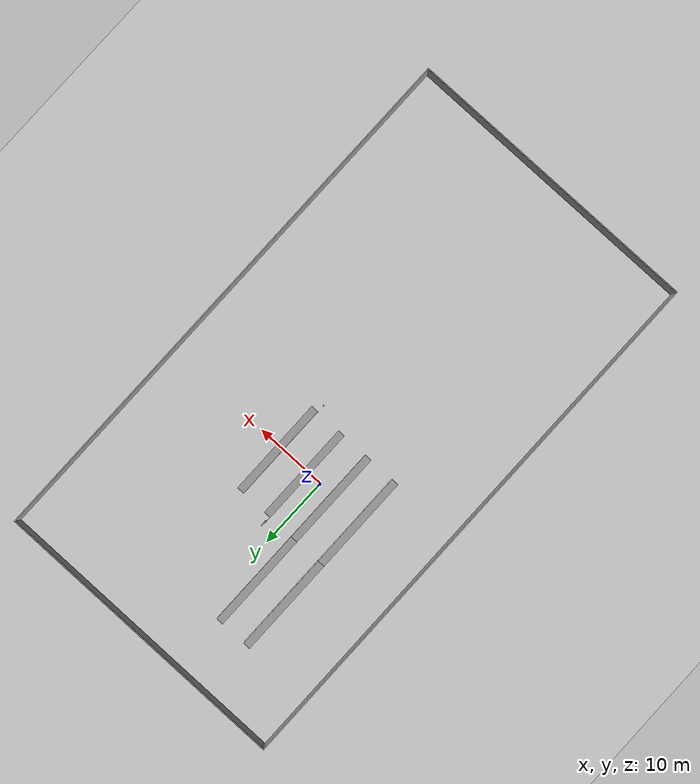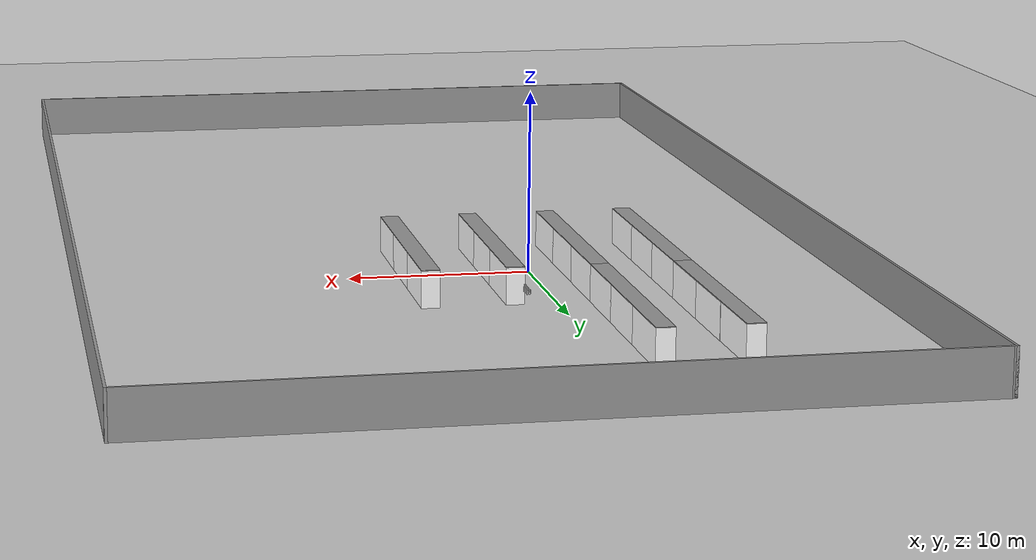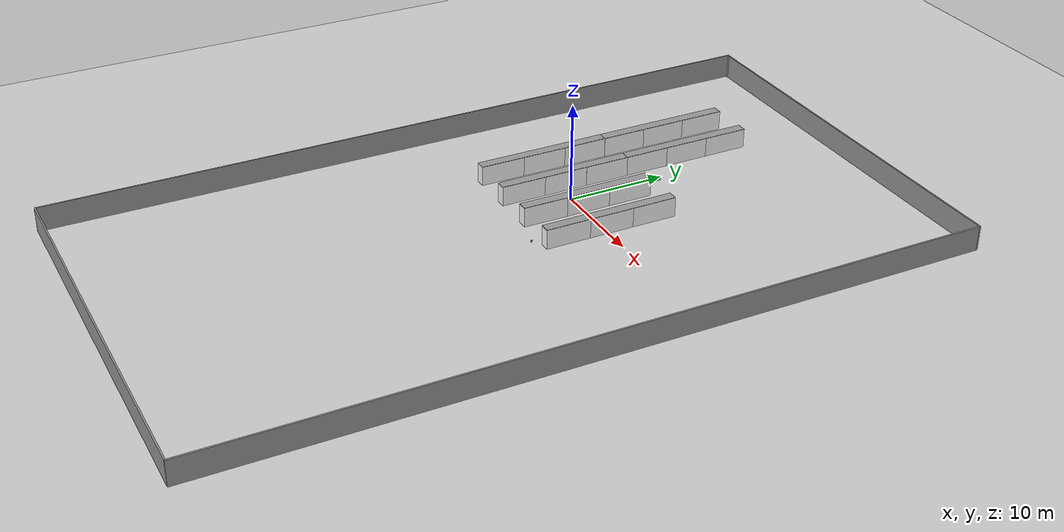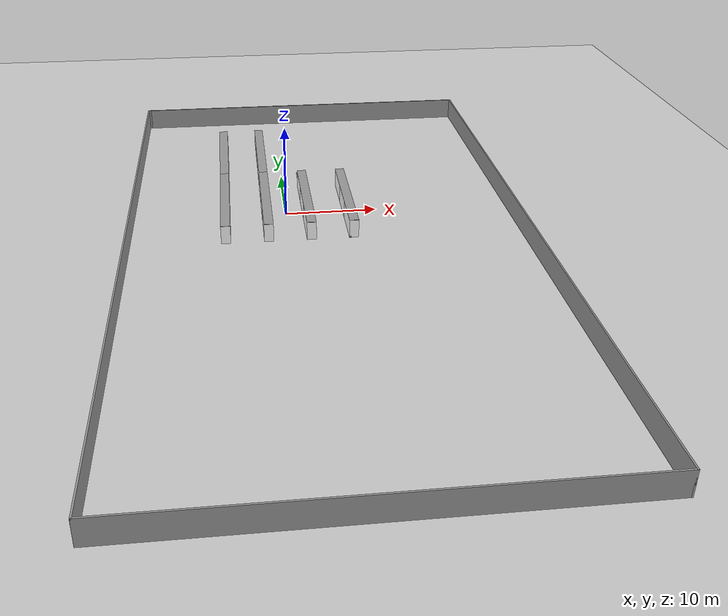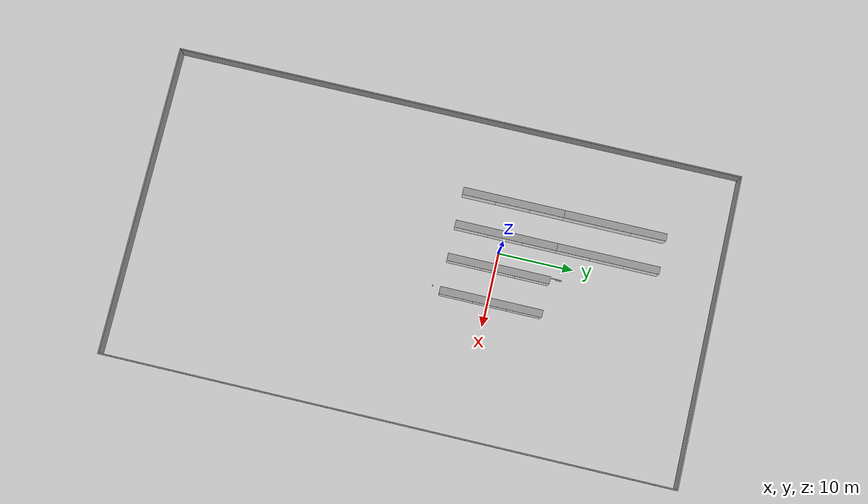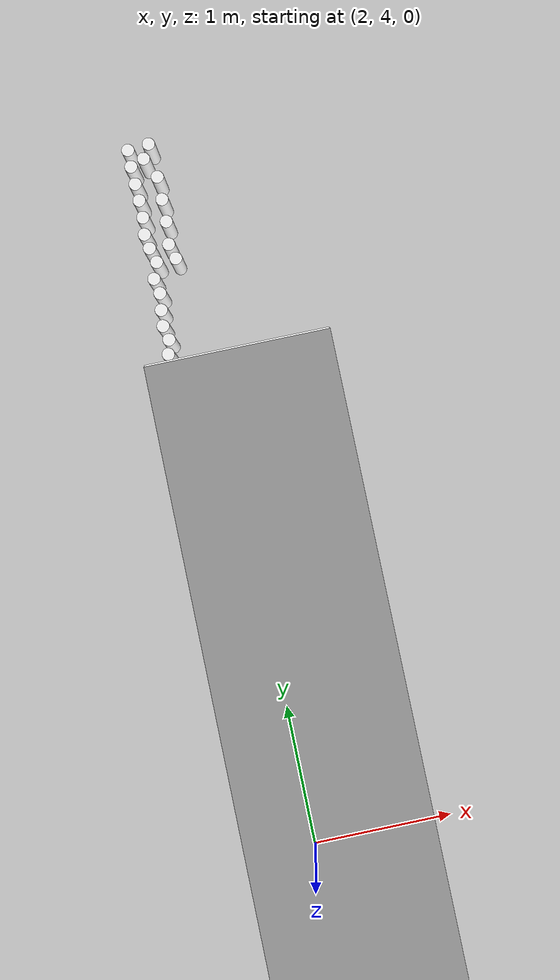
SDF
<sdf version="1.6">
 <world name="default">
  <light name="sun" type="directional">
   <pose>0 0 10 0 -0 0</pose>
   <diffuse>0.8 0.8 0.8 1</diffuse>
   <specular>0.2 0.2 0.2 1</specular>
   <attenuation>
    <range>1000</range>
    <constant>0.9</constant>
    <linear>0.01</linear>
    <quadratic>0.001</quadratic>
   </attenuation>
   <direction>-0.5 0.1 -0.9</direction>
  </light>
  <model name="ground_plane">
   <static>1</static>
   <link name="link">
    <collision name="collision">
     <geometry><plane><normal>0 0 1</normal><size>100 100</size></plane></geometry>
     <surface><friction><ode><mu>100</mu><mu2>50</mu2></ode></friction></surface>
    </collision>
    <visual name="visual">
     <cast_shadows>0</cast_shadows>
     <geometry><plane><normal>0 0 1</normal><size>100 100</size></plane></geometry>
     <material>
      <script><uri>file://media/materials/scripts/gazebo.material</uri><name>Gazebo/Grey</name></script>
     </material>
    </visual>
   </link>
  </model>
  <gravity>0 0 -9.8</gravity>
  <magnetic_field>6e-06 2.3e-05 -4.2e-05</magnetic_field>
  <atmosphere type="adiabatic"/>
  <physics name="default_physics" default="0" type="ode">
   <max_step_size>0.001</max_step_size>
   <real_time_factor>1</real_time_factor>
   <real_time_update_rate>1000</real_time_update_rate>
  </physics>
  <scene><ambient>0.4 0.4 0.4 1</ambient><background>0.7 0.7 0.7 1</background><shadows>1</shadows></scene>
  <spherical_coordinates>
   <surface_model>EARTH_WGS84</surface_model>
   <latitude_deg>0</latitude_deg>
   <longitude_deg>0</longitude_deg>
   <elevation>0</elevation>
   <heading_deg>0</heading_deg>
  </spherical_coordinates>
  <model name="market_aisle_clone">
   <link name="link_0">
    <inertial>
     <mass>45.3865</mass>
     <inertia><ixx>668.696</ixx><ixy>0</ixy><ixz>0</ixz><iyy>41.6273</iyy><iyz>0</iyz><izz>636.647</izz></inertia>
    </inertial>
    <visual name="visual">
     <material>
      <script>
       <uri>model://market_aisle/materials/scripts</uri>
       <uri>model://market_aisle/materials/textures</uri>
       <name>market_aisle/Picture</name>
      </script>
      <shader type="pixel"><normal_map>__default__</normal_map></shader>
      <ambient>1 1 1 1</ambient>
      <diffuse>1 1 1 1</diffuse>
      <specular>0 0 0 1</specular>
      <emissive>0 0 0 1</emissive>
     </material>
     <geometry><box><size>1 4.57035 2</size></box></geometry>
    </visual>
    <collision name="collision">
     <geometry><box><size>1 4.57035 2</size></box></geometry>
     <surface>
      <friction>
       <ode><mu>1</mu><mu2>1</mu2><fdir1>0 0 0</fdir1><slip1>0</slip1><slip2>0</slip2></ode>
       <torsional>
        <coefficient>1</coefficient>
        <patch_radius>0</patch_radius>
        <surface_radius>0</surface_radius>
        <use_patch_radius>1</use_patch_radius>
        <ode><slip>0</slip></ode>
       </torsional>
      </friction>
      <bounce><restitution_coefficient>0</restitution_coefficient><threshold>1e+06</threshold></bounce>
      <contact>
       <collide_without_contact>0</collide_without_contact>
       <collide_without_contact_bitmask>1</collide_without_contact_bitmask>
       <collide_bitmask>1</collide_bitmask>
       <ode>
        <soft_cfm>0</soft_cfm>
        <soft_erp>0.2</soft_erp>
        <kp>1e+13</kp>
        <kd>1</kd>
        <max_vel>0.01</max_vel>
        <min_depth>0</min_depth>
       </ode>
       <bullet>
        <split_impulse>1</split_impulse>
        <split_impulse_penetration_threshold>-0.01</split_impulse_penetration_threshold>
        <soft_cfm>0</soft_cfm>
        <soft_erp>0.2</soft_erp>
        <kp>1e+13</kp>
        <kd>1</kd>
       </bullet>
      </contact>
     </surface>
    </collision>
   </link>
   <static>1</static>
   <pose>-2.25 -4.17401 1 0 -0 0</pose>
  </model>
  <model name="market_aisle_clone_0">
   <link name="link_0">
    <inertial>
     <mass>45.3865</mass>
     <inertia><ixx>668.696</ixx><ixy>0</ixy><ixz>0</ixz><iyy>41.6273</iyy><iyz>0</iyz><izz>636.647</izz></inertia>
    </inertial>
    <visual name="visual">
     <material>
      <script>
       <uri>model://market_aisle/materials/scripts</uri>
       <uri>model://market_aisle/materials/textures</uri>
       <name>market_aisle/Picture</name>
      </script>
      <shader type="pixel"><normal_map>__default__</normal_map></shader>
      <ambient>1 1 1 1</ambient>
      <diffuse>1 1 1 1</diffuse>
      <specular>0 0 0 1</specular>
      <emissive>0 0 0 1</emissive>
     </material>
     <geometry><box><size>1 4.57035 2</size></box></geometry>
    </visual>
    <collision name="collision">
     <geometry><box><size>1 4.57035 2</size></box></geometry>
     <surface>
      <friction>
       <ode><mu>1</mu><mu2>1</mu2><fdir1>0 0 0</fdir1><slip1>0</slip1><slip2>0</slip2></ode>
       <torsional>
        <coefficient>1</coefficient>
        <patch_radius>0</patch_radius>
        <surface_radius>0</surface_radius>
        <use_patch_radius>1</use_patch_radius>
        <ode><slip>0</slip></ode>
       </torsional>
      </friction>
      <bounce><restitution_coefficient>0</restitution_coefficient><threshold>1e+06</threshold></bounce>
      <contact>
       <collide_without_contact>0</collide_without_contact>
       <collide_without_contact_bitmask>1</collide_without_contact_bitmask>
       <collide_bitmask>1</collide_bitmask>
       <ode>
        <soft_cfm>0</soft_cfm>
        <soft_erp>0.2</soft_erp>
        <kp>1e+13</kp>
        <kd>1</kd>
        <max_vel>0.01</max_vel>
        <min_depth>0</min_depth>
       </ode>
       <bullet>
        <split_impulse>1</split_impulse>
        <split_impulse_penetration_threshold>-0.01</split_impulse_penetration_threshold>
        <soft_cfm>0</soft_cfm>
        <soft_erp>0.2</soft_erp>
        <kp>1e+13</kp>
        <kd>1</kd>
       </bullet>
      </contact>
     </surface>
    </collision>
   </link>
   <static>1</static>
   <pose>-2.25 4.953 1 0 -0 0</pose>
  </model>
  <model name="market_aisle_clone1">
   <link name="link_0">
    <inertial>
     <mass>45.3865</mass>
     <inertia><ixx>668.696</ixx><ixy>0</ixy><ixz>0</ixz><iyy>41.6273</iyy><iyz>0</iyz><izz>636.647</izz></inertia>
    </inertial>
    <visual name="visual">
     <material>
      <script>
       <uri>model://market_aisle/materials/scripts</uri>
       <uri>model://market_aisle/materials/textures</uri>
       <name>market_aisle/Picture</name>
      </script>
      <shader type="pixel"><normal_map>__default__</normal_map></shader>
      <ambient>1 1 1 1</ambient>
      <diffuse>1 1 1 1</diffuse>
      <specular>0 0 0 1</specular>
      <emissive>0 0 0 1</emissive>
     </material>
     <geometry><box><size>1 4.57035 2</size></box></geometry>
    </visual>
    <collision name="collision">
     <geometry><box><size>1 4.57035 2</size></box></geometry>
     <surface>
      <friction>
       <ode><mu>1</mu><mu2>1</mu2><fdir1>0 0 0</fdir1><slip1>0</slip1><slip2>0</slip2></ode>
       <torsional>
        <coefficient>1</coefficient>
        <patch_radius>0</patch_radius>
        <surface_radius>0</surface_radius>
        <use_patch_radius>1</use_patch_radius>
        <ode><slip>0</slip></ode>
       </torsional>
      </friction>
      <bounce><restitution_coefficient>0</restitution_coefficient><threshold>1e+06</threshold></bounce>
      <contact>
       <collide_without_contact>0</collide_without_contact>
       <collide_without_contact_bitmask>1</collide_without_contact_bitmask>
       <collide_bitmask>1</collide_bitmask>
       <ode>
        <soft_cfm>0</soft_cfm>
        <soft_erp>0.2</soft_erp>
        <kp>1e+13</kp>
        <kd>1</kd>
        <max_vel>0.01</max_vel>
        <min_depth>0</min_depth>
       </ode>
       <bullet>
        <split_impulse>1</split_impulse>
        <split_impulse_penetration_threshold>-0.01</split_impulse_penetration_threshold>
        <soft_cfm>0</soft_cfm>
        <soft_erp>0.2</soft_erp>
        <kp>1e+13</kp>
        <kd>1</kd>
       </bullet>
      </contact>
     </surface>
    </collision>
   </link>
   <static>1</static>
   <pose>2.25 -4.17401 1 0 -0 0</pose>
  </model>
  <model name="market_aisle_clone_01">
   <link name="link_0">
    <inertial>
     <mass>45.3865</mass>
     <inertia><ixx>668.696</ixx><ixy>0</ixy><ixz>0</ixz><iyy>41.6273</iyy><iyz>0</iyz><izz>636.647</izz></inertia>
    </inertial>
    <visual name="visual">
     <material>
      <script>
       <uri>model://market_aisle/materials/scripts</uri>
       <uri>model://market_aisle/materials/textures</uri>
       <name>market_aisle/Picture</name>
      </script>
      <shader type="pixel"><normal_map>__default__</normal_map></shader>
      <ambient>1 1 1 1</ambient>
      <diffuse>1 1 1 1</diffuse>
      <specular>0 0 0 1</specular>
      <emissive>0 0 0 1</emissive>
     </material>
     <geometry><box><size>1 4.57035 2</size></box></geometry>
    </visual>
    <collision name="collision">
     <geometry><box><size>1 4.57035 2</size></box></geometry>
     <surface>
      <friction>
       <ode><mu>1</mu><mu2>1</mu2><fdir1>0 0 0</fdir1><slip1>0</slip1><slip2>0</slip2></ode>
       <torsional>
        <coefficient>1</coefficient>
        <patch_radius>0</patch_radius>
        <surface_radius>0</surface_radius>
        <use_patch_radius>1</use_patch_radius>
        <ode><slip>0</slip></ode>
       </torsional>
      </friction>
      <bounce><restitution_coefficient>0</restitution_coefficient><threshold>1e+06</threshold></bounce>
      <contact>
       <collide_without_contact>0</collide_without_contact>
       <collide_without_contact_bitmask>1</collide_without_contact_bitmask>
       <collide_bitmask>1</collide_bitmask>
       <ode>
        <soft_cfm>0</soft_cfm>
        <soft_erp>0.2</soft_erp>
        <kp>1e+13</kp>
        <kd>1</kd>
        <max_vel>0.01</max_vel>
        <min_depth>0</min_depth>
       </ode>
       <bullet>
        <split_impulse>1</split_impulse>
        <split_impulse_penetration_threshold>-0.01</split_impulse_penetration_threshold>
        <soft_cfm>0</soft_cfm>
        <soft_erp>0.2</soft_erp>
        <kp>1e+13</kp>
        <kd>1</kd>
       </bullet>
      </contact>
     </surface>
    </collision>
   </link>
   <static>1</static>
   <pose>2.25 4.953 1 0 -0 0</pose>
  </model>
  <model name="market_aisle_clone2">
   <link name="link_0">
    <inertial>
     <mass>45.3865</mass>
     <inertia><ixx>668.696</ixx><ixy>0</ixy><ixz>0</ixz><iyy>41.6273</iyy><iyz>0</iyz><izz>636.647</izz></inertia>
    </inertial>
    <visual name="visual">
     <material>
      <script>
       <uri>model://market_aisle/materials/scripts</uri>
       <uri>model://market_aisle/materials/textures</uri>
       <name>market_aisle/Picture</name>
      </script>
      <shader type="pixel"><normal_map>__default__</normal_map></shader>
      <ambient>1 1 1 1</ambient>
      <diffuse>1 1 1 1</diffuse>
      <specular>0 0 0 1</specular>
      <emissive>0 0 0 1</emissive>
     </material>
     <geometry><box><size>1 4.57035 2</size></box></geometry>
    </visual>
    <collision name="collision">
     <geometry><box><size>1 4.57035 2</size></box></geometry>
     <surface>
      <friction>
       <ode><mu>1</mu><mu2>1</mu2><fdir1>0 0 0</fdir1><slip1>0</slip1><slip2>0</slip2></ode>
       <torsional>
        <coefficient>1</coefficient>
        <patch_radius>0</patch_radius>
        <surface_radius>0</surface_radius>
        <use_patch_radius>1</use_patch_radius>
        <ode><slip>0</slip></ode>
       </torsional>
      </friction>
      <bounce><restitution_coefficient>0</restitution_coefficient><threshold>1e+06</threshold></bounce>
      <contact>
       <collide_without_contact>0</collide_without_contact>
       <collide_without_contact_bitmask>1</collide_without_contact_bitmask>
       <collide_bitmask>1</collide_bitmask>
       <ode>
        <soft_cfm>0</soft_cfm>
        <soft_erp>0.2</soft_erp>
        <kp>1e+13</kp>
        <kd>1</kd>
        <max_vel>0.01</max_vel>
        <min_depth>0</min_depth>
       </ode>
       <bullet>
        <split_impulse>1</split_impulse>
        <split_impulse_penetration_threshold>-0.01</split_impulse_penetration_threshold>
        <soft_cfm>0</soft_cfm>
        <soft_erp>0.2</soft_erp>
        <kp>1e+13</kp>
        <kd>1</kd>
       </bullet>
      </contact>
     </surface>
    </collision>
   </link>
   <static>1</static>
   <pose>6.75 -4.17401 1 0 -0 0</pose>
  </model>
  <model name="market_aisle_clone_02">
   <link name="link_0">
    <inertial>
     <mass>45.3865</mass>
     <inertia><ixx>668.696</ixx><ixy>0</ixy><ixz>0</ixz><iyy>41.6273</iyy><iyz>0</iyz><izz>636.647</izz></inertia>
    </inertial>
    <visual name="visual">
     <material>
      <script>
       <uri>model://market_aisle/materials/scripts</uri>
       <uri>model://market_aisle/materials/textures</uri>
       <name>market_aisle/Picture</name>
      </script>
      <shader type="pixel"><normal_map>__default__</normal_map></shader>
      <ambient>1 1 1 1</ambient>
      <diffuse>1 1 1 1</diffuse>
      <specular>0 0 0 1</specular>
      <emissive>0 0 0 1</emissive>
     </material>
     <geometry><box><size>1 4.57035 2</size></box></geometry>
    </visual>
    <collision name="collision">
     <geometry><box><size>1 4.57035 2</size></box></geometry>
     <surface>
      <friction>
       <ode><mu>1</mu><mu2>1</mu2><fdir1>0 0 0</fdir1><slip1>0</slip1><slip2>0</slip2></ode>
       <torsional>
        <coefficient>1</coefficient>
        <patch_radius>0</patch_radius>
        <surface_radius>0</surface_radius>
        <use_patch_radius>1</use_patch_radius>
        <ode><slip>0</slip></ode>
       </torsional>
      </friction>
      <bounce><restitution_coefficient>0</restitution_coefficient><threshold>1e+06</threshold></bounce>
      <contact>
       <collide_without_contact>0</collide_without_contact>
       <collide_without_contact_bitmask>1</collide_without_contact_bitmask>
       <collide_bitmask>1</collide_bitmask>
       <ode>
        <soft_cfm>0</soft_cfm>
        <soft_erp>0.2</soft_erp>
        <kp>1e+13</kp>
        <kd>1</kd>
        <max_vel>0.01</max_vel>
        <min_depth>0</min_depth>
       </ode>
       <bullet>
        <split_impulse>1</split_impulse>
        <split_impulse_penetration_threshold>-0.01</split_impulse_penetration_threshold>
        <soft_cfm>0</soft_cfm>
        <soft_erp>0.2</soft_erp>
        <kp>1e+13</kp>
        <kd>1</kd>
       </bullet>
      </contact>
     </surface>
    </collision>
   </link>
   <static>1</static>
   <pose>6.75 4.953 1 0 -0 0</pose>
  </model>
  <model name="market_aisle_clone3">
   <link name="link_0">
    <inertial>
     <mass>45.3865</mass>
     <inertia><ixx>668.696</ixx><ixy>0</ixy><ixz>0</ixz><iyy>41.6273</iyy><iyz>0</iyz><izz>636.647</izz></inertia>
    </inertial>
    <visual name="visual">
     <material>
      <script>
       <uri>model://market_aisle/materials/scripts</uri>
       <uri>model://market_aisle/materials/textures</uri>
       <name>market_aisle/Picture</name>
      </script>
      <shader type="pixel"><normal_map>__default__</normal_map></shader>
      <ambient>1 1 1 1</ambient>
      <diffuse>1 1 1 1</diffuse>
      <specular>0 0 0 1</specular>
      <emissive>0 0 0 1</emissive>
     </material>
     <geometry><box><size>1 4.57035 2</size></box></geometry>
    </visual>
    <collision name="collision">
     <geometry><box><size>1 4.57035 2</size></box></geometry>
     <surface>
      <friction>
       <ode><mu>1</mu><mu2>1</mu2><fdir1>0 0 0</fdir1><slip1>0</slip1><slip2>0</slip2></ode>
       <torsional>
        <coefficient>1</coefficient>
        <patch_radius>0</patch_radius>
        <surface_radius>0</surface_radius>
        <use_patch_radius>1</use_patch_radius>
        <ode><slip>0</slip></ode>
       </torsional>
      </friction>
      <bounce><restitution_coefficient>0</restitution_coefficient><threshold>1e+06</threshold></bounce>
      <contact>
       <collide_without_contact>0</collide_without_contact>
       <collide_without_contact_bitmask>1</collide_without_contact_bitmask>
       <collide_bitmask>1</collide_bitmask>
       <ode>
        <soft_cfm>0</soft_cfm>
        <soft_erp>0.2</soft_erp>
        <kp>1e+13</kp>
        <kd>1</kd>
        <max_vel>0.01</max_vel>
        <min_depth>0</min_depth>
       </ode>
       <bullet>
        <split_impulse>1</split_impulse>
        <split_impulse_penetration_threshold>-0.01</split_impulse_penetration_threshold>
        <soft_cfm>0</soft_cfm>
        <soft_erp>0.2</soft_erp>
        <kp>1e+13</kp>
        <kd>1</kd>
       </bullet>
      </contact>
     </surface>
    </collision>
   </link>
   <static>1</static>
   <pose>-6.75 -4.17401 1 0 -0 0</pose>
  </model>
  <model name="market_aisle_clone_03">
   <link name="link_0">
    <inertial>
     <mass>45.3865</mass>
     <inertia><ixx>668.696</ixx><ixy>0</ixy><ixz>0</ixz><iyy>41.6273</iyy><iyz>0</iyz><izz>636.647</izz></inertia>
    </inertial>
    <visual name="visual">
     <material>
      <script>
       <uri>model://market_aisle/materials/scripts</uri>
       <uri>model://market_aisle/materials/textures</uri>
       <name>market_aisle/Picture</name>
      </script>
      <shader type="pixel"><normal_map>__default__</normal_map></shader>
      <ambient>1 1 1 1</ambient>
      <diffuse>1 1 1 1</diffuse>
      <specular>0 0 0 1</specular>
      <emissive>0 0 0 1</emissive>
     </material>
     <geometry><box><size>1 4.57035 2</size></box></geometry>
    </visual>
    <collision name="collision">
     <geometry><box><size>1 4.57035 2</size></box></geometry>
     <surface>
      <friction>
       <ode><mu>1</mu><mu2>1</mu2><fdir1>0 0 0</fdir1><slip1>0</slip1><slip2>0</slip2></ode>
       <torsional>
        <coefficient>1</coefficient>
        <patch_radius>0</patch_radius>
        <surface_radius>0</surface_radius>
        <use_patch_radius>1</use_patch_radius>
        <ode><slip>0</slip></ode>
       </torsional>
      </friction>
      <bounce><restitution_coefficient>0</restitution_coefficient><threshold>1e+06</threshold></bounce>
      <contact>
       <collide_without_contact>0</collide_without_contact>
       <collide_without_contact_bitmask>1</collide_without_contact_bitmask>
       <collide_bitmask>1</collide_bitmask>
       <ode>
        <soft_cfm>0</soft_cfm>
        <soft_erp>0.2</soft_erp>
        <kp>1e+13</kp>
        <kd>1</kd>
        <max_vel>0.01</max_vel>
        <min_depth>0</min_depth>
       </ode>
       <bullet>
        <split_impulse>1</split_impulse>
        <split_impulse_penetration_threshold>-0.01</split_impulse_penetration_threshold>
        <soft_cfm>0</soft_cfm>
        <soft_erp>0.2</soft_erp>
        <kp>1e+13</kp>
        <kd>1</kd>
       </bullet>
      </contact>
     </surface>
    </collision>
   </link>
   <static>1</static>
   <pose>-6.75 4.953 1 0 -0 0</pose>
  </model>
  <model name="market_aisle_clone1_clone">
   <link name="link_0">
    <inertial>
     <mass>45.3865</mass>
     <inertia><ixx>668.696</ixx><ixy>0</ixy><ixz>0</ixz><iyy>41.6273</iyy><iyz>0</iyz><izz>636.647</izz></inertia>
    </inertial>
    <visual name="visual">
     <material>
      <script>
       <uri>model://market_aisle/materials/scripts</uri>
       <uri>model://market_aisle/materials/textures</uri>
       <name>market_aisle/Picture</name>
      </script>
      <shader type="pixel"><normal_map>__default__</normal_map></shader>
      <ambient>1 1 1 1</ambient>
      <diffuse>1 1 1 1</diffuse>
      <specular>0 0 0 1</specular>
      <emissive>0 0 0 1</emissive>
     </material>
     <geometry><box><size>1 4.57035 2</size></box></geometry>
    </visual>
    <collision name="collision">
     <geometry><box><size>1 4.57035 2</size></box></geometry>
     <surface>
      <friction>
       <ode><mu>1</mu><mu2>1</mu2><fdir1>0 0 0</fdir1><slip1>0</slip1><slip2>0</slip2></ode>
       <torsional>
        <coefficient>1</coefficient>
        <patch_radius>0</patch_radius>
        <surface_radius>0</surface_radius>
        <use_patch_radius>1</use_patch_radius>
        <ode><slip>0</slip></ode>
       </torsional>
      </friction>
      <bounce><restitution_coefficient>0</restitution_coefficient><threshold>1e+06</threshold></bounce>
      <contact>
       <collide_without_contact>0</collide_without_contact>
       <collide_without_contact_bitmask>1</collide_without_contact_bitmask>
       <collide_bitmask>1</collide_bitmask>
       <ode>
        <soft_cfm>0</soft_cfm>
        <soft_erp>0.2</soft_erp>
        <kp>1e+13</kp>
        <kd>1</kd>
        <max_vel>0.01</max_vel>
        <min_depth>0</min_depth>
       </ode>
       <bullet>
        <split_impulse>1</split_impulse>
        <split_impulse_penetration_threshold>-0.01</split_impulse_penetration_threshold>
        <soft_cfm>0</soft_cfm>
        <soft_erp>0.2</soft_erp>
        <kp>1e+13</kp>
        <kd>1</kd>
       </bullet>
      </contact>
     </surface>
    </collision>
   </link>
   <static>1</static>
   <pose>2.25 0.385462 1 0 -0 0</pose>
  </model>
  <model name="market_aisle_clone1_clone_0">
   <link name="link_0">
    <inertial>
     <mass>45.3865</mass>
     <inertia><ixx>668.696</ixx><ixy>0</ixy><ixz>0</ixz><iyy>41.6273</iyy><iyz>0</iyz><izz>636.647</izz></inertia>
    </inertial>
    <visual name="visual">
     <material>
      <script>
       <uri>model://market_aisle/materials/scripts</uri>
       <uri>model://market_aisle/materials/textures</uri>
       <name>market_aisle/Picture</name>
      </script>
      <shader type="pixel"><normal_map>__default__</normal_map></shader>
      <ambient>1 1 1 1</ambient>
      <diffuse>1 1 1 1</diffuse>
      <specular>0 0 0 1</specular>
      <emissive>0 0 0 1</emissive>
     </material>
     <geometry><box><size>1 4.57035 2</size></box></geometry>
    </visual>
    <collision name="collision">
     <geometry><box><size>1 4.57035 2</size></box></geometry>
     <surface>
      <friction>
       <ode><mu>1</mu><mu2>1</mu2><fdir1>0 0 0</fdir1><slip1>0</slip1><slip2>0</slip2></ode>
       <torsional>
        <coefficient>1</coefficient>
        <patch_radius>0</patch_radius>
        <surface_radius>0</surface_radius>
        <use_patch_radius>1</use_patch_radius>
        <ode><slip>0</slip></ode>
       </torsional>
      </friction>
      <bounce><restitution_coefficient>0</restitution_coefficient><threshold>1e+06</threshold></bounce>
      <contact>
       <collide_without_contact>0</collide_without_contact>
       <collide_without_contact_bitmask>1</collide_without_contact_bitmask>
       <collide_bitmask>1</collide_bitmask>
       <ode>
        <soft_cfm>0</soft_cfm>
        <soft_erp>0.2</soft_erp>
        <kp>1e+13</kp>
        <kd>1</kd>
        <max_vel>0.01</max_vel>
        <min_depth>0</min_depth>
       </ode>
       <bullet>
        <split_impulse>1</split_impulse>
        <split_impulse_penetration_threshold>-0.01</split_impulse_penetration_threshold>
        <soft_cfm>0</soft_cfm>
        <soft_erp>0.2</soft_erp>
        <kp>1e+13</kp>
        <kd>1</kd>
       </bullet>
      </contact>
     </surface>
    </collision>
   </link>
   <static>1</static>
   <pose>-2.25 0.377509 1 0 -0 0</pose>
  </model>
  <model name="market_aisle_clone1_clone_1">
   <link name="link_0">
    <inertial>
     <mass>45.3865</mass>
     <inertia><ixx>668.696</ixx><ixy>0</ixy><ixz>0</ixz><iyy>41.6273</iyy><iyz>0</iyz><izz>636.647</izz></inertia>
    </inertial>
    <visual name="visual">
     <material>
      <script>
       <uri>model://market_aisle/materials/scripts</uri>
       <uri>model://market_aisle/materials/textures</uri>
       <name>market_aisle/Picture</name>
      </script>
      <shader type="pixel"><normal_map>__default__</normal_map></shader>
      <ambient>1 1 1 1</ambient>
      <diffuse>1 1 1 1</diffuse>
      <specular>0 0 0 1</specular>
      <emissive>0 0 0 1</emissive>
     </material>
     <geometry><box><size>1 4.57035 2</size></box></geometry>
    </visual>
    <collision name="collision">
     <geometry><box><size>1 4.57035 2</size></box></geometry>
     <surface>
      <friction>
       <ode><mu>1</mu><mu2>1</mu2><fdir1>0 0 0</fdir1><slip1>0</slip1><slip2>0</slip2></ode>
       <torsional>
        <coefficient>1</coefficient>
        <patch_radius>0</patch_radius>
        <surface_radius>0</surface_radius>
        <use_patch_radius>1</use_patch_radius>
        <ode><slip>0</slip></ode>
       </torsional>
      </friction>
      <bounce><restitution_coefficient>0</restitution_coefficient><threshold>1e+06</threshold></bounce>
      <contact>
       <collide_without_contact>0</collide_without_contact>
       <collide_without_contact_bitmask>1</collide_without_contact_bitmask>
       <collide_bitmask>1</collide_bitmask>
       <ode>
        <soft_cfm>0</soft_cfm>
        <soft_erp>0.2</soft_erp>
        <kp>1e+13</kp>
        <kd>1</kd>
        <max_vel>0.01</max_vel>
        <min_depth>0</min_depth>
       </ode>
       <bullet>
        <split_impulse>1</split_impulse>
        <split_impulse_penetration_threshold>-0.01</split_impulse_penetration_threshold>
        <soft_cfm>0</soft_cfm>
        <soft_erp>0.2</soft_erp>
        <kp>1e+13</kp>
        <kd>1</kd>
       </bullet>
      </contact>
     </surface>
    </collision>
   </link>
   <static>1</static>
   <pose>-6.75 0.388711 1 0 -0 0</pose>
  </model>
  <model name="market_aisle_clone1_clone_2">
   <link name="link_0">
    <inertial>
     <mass>45.3865</mass>
     <inertia><ixx>668.696</ixx><ixy>0</ixy><ixz>0</ixz><iyy>41.6273</iyy><iyz>0</iyz><izz>636.647</izz></inertia>
    </inertial>
    <visual name="visual">
     <material>
      <script>
       <uri>model://market_aisle/materials/scripts</uri>
       <uri>model://market_aisle/materials/textures</uri>
       <name>market_aisle/Picture</name>
      </script>
      <shader type="pixel"><normal_map>__default__</normal_map></shader>
      <ambient>1 1 1 1</ambient>
      <diffuse>1 1 1 1</diffuse>
      <specular>0 0 0 1</specular>
      <emissive>0 0 0 1</emissive>
     </material>
     <geometry><box><size>1 4.57035 2</size></box></geometry>
    </visual>
    <collision name="collision">
     <geometry><box><size>1 4.57035 2</size></box></geometry>
     <surface>
      <friction>
       <ode><mu>1</mu><mu2>1</mu2><fdir1>0 0 0</fdir1><slip1>0</slip1><slip2>0</slip2></ode>
       <torsional>
        <coefficient>1</coefficient>
        <patch_radius>0</patch_radius>
        <surface_radius>0</surface_radius>
        <use_patch_radius>1</use_patch_radius>
        <ode><slip>0</slip></ode>
       </torsional>
      </friction>
      <bounce><restitution_coefficient>0</restitution_coefficient><threshold>1e+06</threshold></bounce>
      <contact>
       <collide_without_contact>0</collide_without_contact>
       <collide_without_contact_bitmask>1</collide_without_contact_bitmask>
       <collide_bitmask>1</collide_bitmask>
       <ode>
        <soft_cfm>0</soft_cfm>
        <soft_erp>0.2</soft_erp>
        <kp>1e+13</kp>
        <kd>1</kd>
        <max_vel>0.01</max_vel>
        <min_depth>0</min_depth>
       </ode>
       <bullet>
        <split_impulse>1</split_impulse>
        <split_impulse_penetration_threshold>-0.01</split_impulse_penetration_threshold>
        <soft_cfm>0</soft_cfm>
        <soft_erp>0.2</soft_erp>
        <kp>1e+13</kp>
        <kd>1</kd>
       </bullet>
      </contact>
     </surface>
    </collision>
   </link>
   <static>1</static>
   <pose>6.75 0.394789 1 0 -0 0</pose>
  </model>
  <model name="cocacola">
   <static>0</static>
   <link name="link">
    <inertial>
     <mass>0.125</mass>
     <inertia><ixx>0</ixx><ixy>0</ixy><ixz>0</ixz><iyy>0</iyy><iyz>0</iyz><izz>0</izz></inertia>
    </inertial>
    <collision name="collision">
     <pose>0 0 0.075 -3.14159 -0 0</pose>
     <geometry><cylinder><radius>0.04</radius><length>0.15</length></cylinder></geometry>
    </collision>
    <visual name="visual">
     <pose>0 0 0.075 -3.14159 -0 0</pose>
     <geometry><cylinder><radius>0.04</radius><length>0.15</length></cylinder></geometry>
     <material>
      <script>
       <uri>model://cocacola/material/scripts</uri>
       <uri>model://cocacola/material/textures</uri>
       <name>Custom/cocacola</name>
      </script>
     </material>
    </visual>
    <velocity_decay><linear>0</linear><angular>0</angular></velocity_decay>
   </link>
   <pose>6.26672 -7.45882 0.559722 -0.003472 0.100888 -0.035064</pose>
  </model>
  <model name="cocacola_clone">
   <static>0</static>
   <link name="link">
    <inertial>
     <mass>0.125</mass>
     <inertia><ixx>0</ixx><ixy>0</ixy><ixz>0</ixz><iyy>0</iyy><iyz>0</iyz><izz>0</izz></inertia>
    </inertial>
    <collision name="collision">
     <pose>0 0 0.075 -3.14159 -0 0</pose>
     <geometry><cylinder><radius>0.04</radius><length>0.15</length></cylinder></geometry>
    </collision>
    <visual name="visual">
     <pose>0 0 0.075 -3.14159 -0 0</pose>
     <geometry><cylinder><radius>0.04</radius><length>0.15</length></cylinder></geometry>
     <material>
      <script>
       <uri>model://cocacola/material/scripts</uri>
       <uri>model://cocacola/material/textures</uri>
       <name>Custom/cocacola</name>
      </script>
     </material>
    </visual>
    <velocity_decay><linear>0</linear><angular>0</angular></velocity_decay>
   </link>
   <pose>6.26674 -7.55974 0.559854 0.000678 0.12636 -0.003264</pose>
  </model>
  <model name="cocacola_clone_0">
   <static>0</static>
   <link name="link">
    <inertial>
     <mass>0.125</mass>
     <inertia><ixx>0</ixx><ixy>0</ixy><ixz>0</ixz><iyy>0</iyy><iyz>0</iyz><izz>0</izz></inertia>
    </inertial>
    <collision name="collision">
     <pose>0 0 0.075 -3.14159 -0 0</pose>
     <geometry><cylinder><radius>0.04</radius><length>0.15</length></cylinder></geometry>
    </collision>
    <visual name="visual">
     <pose>0 0 0.075 -3.14159 -0 0</pose>
     <geometry><cylinder><radius>0.04</radius><length>0.15</length></cylinder></geometry>
     <material>
      <script>
       <uri>model://cocacola/material/scripts</uri>
       <uri>model://cocacola/material/textures</uri>
       <name>Custom/cocacola</name>
      </script>
     </material>
    </visual>
    <velocity_decay><linear>0</linear><angular>0</angular></velocity_decay>
   </link>
   <pose>6.18345 -7.46173 0.569353 -0.003199 0.126342 -0.048477</pose>
  </model>
  <model name="cocacola_clone_1">
   <static>0</static>
   <link name="link">
    <inertial>
     <mass>0.125</mass>
     <inertia><ixx>0</ixx><ixy>0</ixy><ixz>0</ixz><iyy>0</iyy><iyz>0</iyz><izz>0</izz></inertia>
    </inertial>
    <collision name="collision">
     <pose>0 0 0.075 -3.14159 -0 0</pose>
     <geometry><cylinder><radius>0.04</radius><length>0.15</length></cylinder></geometry>
    </collision>
    <visual name="visual">
     <pose>0 0 0.075 -3.14159 -0 0</pose>
     <geometry><cylinder><radius>0.04</radius><length>0.15</length></cylinder></geometry>
     <material>
      <script>
       <uri>model://cocacola/material/scripts</uri>
       <uri>model://cocacola/material/textures</uri>
       <name>Custom/cocacola</name>
      </script>
     </material>
    </visual>
    <velocity_decay><linear>0</linear><angular>0</angular></velocity_decay>
   </link>
   <pose>6.18723 -7.5568 0.568733 0.002407 0.119071 0.008247</pose>
  </model>
  <model name="asile_top_0">
   <link name="link_0">
    <pose>5e-06 0 -4e-06 0 -0 0</pose>
    <inertial>
     <mass>0.475296</mass>
     <inertia>
      <ixx>7.40524</ixx>
      <ixy>0</ixy>
      <ixz>0</ixz>
      <iyy>0.0496263</iyy>
      <iyz>0</iyz>
      <izz>7.45479</izz>
     </inertia>
    </inertial>
    <visual name="visual">
     <geometry><box><size>1 13.6734 0.031027</size></box></geometry>
     <material>
      <lighting>1</lighting>
      <script><uri>file://media/materials/scripts/gazebo.material</uri><name>Gazebo/Grey</name></script>
      <shader type="pixel"><normal_map>__default__</normal_map></shader>
      <ambient>0.3 0.3 0.3 1</ambient>
      <diffuse>0.7 0.7 0.7 1</diffuse>
      <specular>0.01 0.01 0.01 1</specular>
      <emissive>0 0 0 1</emissive>
     </material>
    </visual>
    <collision name="collision">
     <geometry><box><size>1 13.6734 0.031027</size></box></geometry>
     <surface>
      <friction>
       <ode><mu>1</mu><mu2>1</mu2><fdir1>0 0 0</fdir1><slip1>0</slip1><slip2>0</slip2></ode>
       <torsional>
        <coefficient>1</coefficient>
        <patch_radius>0</patch_radius>
        <surface_radius>0</surface_radius>
        <use_patch_radius>1</use_patch_radius>
        <ode><slip>0</slip></ode>
       </torsional>
      </friction>
      <bounce><restitution_coefficient>0</restitution_coefficient><threshold>1e+06</threshold></bounce>
      <contact>
       <collide_without_contact>0</collide_without_contact>
       <collide_without_contact_bitmask>1</collide_without_contact_bitmask>
       <collide_bitmask>1</collide_bitmask>
       <ode>
        <soft_cfm>0</soft_cfm>
        <soft_erp>0.2</soft_erp>
        <kp>1e+13</kp>
        <kd>1</kd>
        <max_vel>0.01</max_vel>
        <min_depth>0</min_depth>
       </ode>
       <bullet>
        <split_impulse>1</split_impulse>
        <split_impulse_penetration_threshold>-0.01</split_impulse_penetration_threshold>
        <soft_cfm>0</soft_cfm>
        <soft_erp>0.2</soft_erp>
        <kp>1e+13</kp>
        <kd>1</kd>
       </bullet>
      </contact>
     </surface>
    </collision>
   </link>
   <static>1</static>
   <pose>-6.75 0.384568 2.02165 0 -0 0</pose>
  </model>
  <model name="asile_top">
   <link name="link_0">
    <pose>5e-06 0 -4e-06 0 -0 0</pose>
    <inertial>
     <mass>0.475296</mass>
     <inertia>
      <ixx>7.40524</ixx>
      <ixy>0</ixy>
      <ixz>0</ixz>
      <iyy>0.0496263</iyy>
      <iyz>0</iyz>
      <izz>7.45479</izz>
     </inertia>
    </inertial>
    <visual name="visual">
     <geometry><box><size>1 13.6734 0.031027</size></box></geometry>
     <material>
      <lighting>1</lighting>
      <script><uri>file://media/materials/scripts/gazebo.material</uri><name>Gazebo/Grey</name></script>
      <shader type="pixel"><normal_map>__default__</normal_map></shader>
      <ambient>0.3 0.3 0.3 1</ambient>
      <diffuse>0.7 0.7 0.7 1</diffuse>
      <specular>0.01 0.01 0.01 1</specular>
      <emissive>0 0 0 1</emissive>
     </material>
    </visual>
    <collision name="collision">
     <geometry><box><size>1 13.6734 0.031027</size></box></geometry>
     <surface>
      <friction>
       <ode><mu>1</mu><mu2>1</mu2><fdir1>0 0 0</fdir1><slip1>0</slip1><slip2>0</slip2></ode>
       <torsional>
        <coefficient>1</coefficient>
        <patch_radius>0</patch_radius>
        <surface_radius>0</surface_radius>
        <use_patch_radius>1</use_patch_radius>
        <ode><slip>0</slip></ode>
       </torsional>
      </friction>
      <bounce><restitution_coefficient>0</restitution_coefficient><threshold>1e+06</threshold></bounce>
      <contact>
       <collide_without_contact>0</collide_without_contact>
       <collide_without_contact_bitmask>1</collide_without_contact_bitmask>
       <collide_bitmask>1</collide_bitmask>
       <ode>
        <soft_cfm>0</soft_cfm>
        <soft_erp>0.2</soft_erp>
        <kp>1e+13</kp>
        <kd>1</kd>
        <max_vel>0.01</max_vel>
        <min_depth>0</min_depth>
       </ode>
       <bullet>
        <split_impulse>1</split_impulse>
        <split_impulse_penetration_threshold>-0.01</split_impulse_penetration_threshold>
        <soft_cfm>0</soft_cfm>
        <soft_erp>0.2</soft_erp>
        <kp>1e+13</kp>
        <kd>1</kd>
       </bullet>
      </contact>
     </surface>
    </collision>
   </link>
   <static>1</static>
   <pose>-2.25 0.384568 2.02165 0 -0 0</pose>
  </model>
  <model name="asile_top_1">
   <link name="link_0">
    <pose>5e-06 0 -4e-06 0 -0 0</pose>
    <inertial>
     <mass>0.475296</mass>
     <inertia>
      <ixx>7.40524</ixx>
      <ixy>0</ixy>
      <ixz>0</ixz>
      <iyy>0.0496263</iyy>
      <iyz>0</iyz>
      <izz>7.45479</izz>
     </inertia>
    </inertial>
    <visual name="visual">
     <geometry><box><size>1 13.6734 0.031027</size></box></geometry>
     <material>
      <lighting>1</lighting>
      <script><uri>file://media/materials/scripts/gazebo.material</uri><name>Gazebo/Grey</name></script>
      <shader type="pixel"><normal_map>__default__</normal_map></shader>
      <ambient>0.3 0.3 0.3 1</ambient>
      <diffuse>0.7 0.7 0.7 1</diffuse>
      <specular>0.01 0.01 0.01 1</specular>
      <emissive>0 0 0 1</emissive>
     </material>
    </visual>
    <collision name="collision">
     <geometry><box><size>1 13.6734 0.031027</size></box></geometry>
     <surface>
      <friction>
       <ode><mu>1</mu><mu2>1</mu2><fdir1>0 0 0</fdir1><slip1>0</slip1><slip2>0</slip2></ode>
       <torsional>
        <coefficient>1</coefficient>
        <patch_radius>0</patch_radius>
        <surface_radius>0</surface_radius>
        <use_patch_radius>1</use_patch_radius>
        <ode><slip>0</slip></ode>
       </torsional>
      </friction>
      <bounce><restitution_coefficient>0</restitution_coefficient><threshold>1e+06</threshold></bounce>
      <contact>
       <collide_without_contact>0</collide_without_contact>
       <collide_without_contact_bitmask>1</collide_without_contact_bitmask>
       <collide_bitmask>1</collide_bitmask>
       <ode>
        <soft_cfm>0</soft_cfm>
        <soft_erp>0.2</soft_erp>
        <kp>1e+13</kp>
        <kd>1</kd>
        <max_vel>0.01</max_vel>
        <min_depth>0</min_depth>
       </ode>
       <bullet>
        <split_impulse>1</split_impulse>
        <split_impulse_penetration_threshold>-0.01</split_impulse_penetration_threshold>
        <soft_cfm>0</soft_cfm>
        <soft_erp>0.2</soft_erp>
        <kp>1e+13</kp>
        <kd>1</kd>
       </bullet>
      </contact>
     </surface>
    </collision>
   </link>
   <static>1</static>
   <pose>2.25 0.384568 2.02165 0 -0 0</pose>
  </model>
  <model name="asile_top_2">
   <link name="link_0">
    <pose>5e-06 0 -4e-06 0 -0 0</pose>
    <inertial>
     <mass>0.475296</mass>
     <inertia>
      <ixx>7.40524</ixx>
      <ixy>0</ixy>
      <ixz>0</ixz>
      <iyy>0.0496263</iyy>
      <iyz>0</iyz>
      <izz>7.45479</izz>
     </inertia>
    </inertial>
    <visual name="visual">
     <geometry><box><size>1 13.6734 0.031027</size></box></geometry>
     <material>
      <lighting>1</lighting>
      <script><uri>file://media/materials/scripts/gazebo.material</uri><name>Gazebo/Grey</name></script>
      <shader type="pixel"><normal_map>__default__</normal_map></shader>
      <ambient>0.3 0.3 0.3 1</ambient>
      <diffuse>0.7 0.7 0.7 1</diffuse>
      <specular>0.01 0.01 0.01 1</specular>
      <emissive>0 0 0 1</emissive>
     </material>
    </visual>
    <collision name="collision">
     <geometry><box><size>1 13.6734 0.031027</size></box></geometry>
     <surface>
      <friction>
       <ode><mu>1</mu><mu2>1</mu2><fdir1>0 0 0</fdir1><slip1>0</slip1><slip2>0</slip2></ode>
       <torsional>
        <coefficient>1</coefficient>
        <patch_radius>0</patch_radius>
        <surface_radius>0</surface_radius>
        <use_patch_radius>1</use_patch_radius>
        <ode><slip>0</slip></ode>
       </torsional>
      </friction>
      <bounce><restitution_coefficient>0</restitution_coefficient><threshold>1e+06</threshold></bounce>
      <contact>
       <collide_without_contact>0</collide_without_contact>
       <collide_without_contact_bitmask>1</collide_without_contact_bitmask>
       <collide_bitmask>1</collide_bitmask>
       <ode>
        <soft_cfm>0</soft_cfm>
        <soft_erp>0.2</soft_erp>
        <kp>1e+13</kp>
        <kd>1</kd>
        <max_vel>0.01</max_vel>
        <min_depth>0</min_depth>
       </ode>
       <bullet>
        <split_impulse>1</split_impulse>
        <split_impulse_penetration_threshold>-0.01</split_impulse_penetration_threshold>
        <soft_cfm>0</soft_cfm>
        <soft_erp>0.2</soft_erp>
        <kp>1e+13</kp>
        <kd>1</kd>
       </bullet>
      </contact>
     </surface>
    </collision>
   </link>
   <static>1</static>
   <pose>6.75 0.384568 2.02165 0 -0 0</pose>
  </model>
  <model name="market_aisle_clone_03_clone">
   <link name="link_0">
    <inertial>
     <mass>45.3865</mass>
     <inertia><ixx>668.696</ixx><ixy>0</ixy><ixz>0</ixz><iyy>41.6273</iyy><iyz>0</iyz><izz>636.647</izz></inertia>
    </inertial>
    <visual name="visual">
     <material>
      <script>
       <uri>model://market_aisle/materials/scripts</uri>
       <uri>model://market_aisle/materials/textures</uri>
       <name>market_aisle/Picture</name>
      </script>
      <shader type="pixel"><normal_map>__default__</normal_map></shader>
      <ambient>1 1 1 1</ambient>
      <diffuse>1 1 1 1</diffuse>
      <specular>0 0 0 1</specular>
      <emissive>0 0 0 1</emissive>
     </material>
     <geometry><box><size>1 4.57035 2</size></box></geometry>
    </visual>
    <collision name="collision">
     <geometry><box><size>1 4.57035 2</size></box></geometry>
     <surface>
      <friction>
       <ode><mu>1</mu><mu2>1</mu2><fdir1>0 0 0</fdir1><slip1>0</slip1><slip2>0</slip2></ode>
       <torsional>
        <coefficient>1</coefficient>
        <patch_radius>0</patch_radius>
        <surface_radius>0</surface_radius>
        <use_patch_radius>1</use_patch_radius>
        <ode><slip>0</slip></ode>
       </torsional>
      </friction>
      <bounce><restitution_coefficient>0</restitution_coefficient><threshold>1e+06</threshold></bounce>
      <contact>
       <collide_without_contact>0</collide_without_contact>
       <collide_without_contact_bitmask>1</collide_without_contact_bitmask>
       <collide_bitmask>1</collide_bitmask>
       <ode>
        <soft_cfm>0</soft_cfm>
        <soft_erp>0.2</soft_erp>
        <kp>1e+13</kp>
        <kd>1</kd>
        <max_vel>0.01</max_vel>
        <min_depth>0</min_depth>
       </ode>
       <bullet>
        <split_impulse>1</split_impulse>
        <split_impulse_penetration_threshold>-0.01</split_impulse_penetration_threshold>
        <soft_cfm>0</soft_cfm>
        <soft_erp>0.2</soft_erp>
        <kp>1e+13</kp>
        <kd>1</kd>
       </bullet>
      </contact>
     </surface>
    </collision>
   </link>
   <static>1</static>
   <pose>-6.73625 9.51575 1 0 -0 0</pose>
  </model>
  <model name="market_aisle_clone_03_clone_0">
   <link name="link_0">
    <inertial>
     <mass>45.3865</mass>
     <inertia><ixx>668.696</ixx><ixy>0</ixy><ixz>0</ixz><iyy>41.6273</iyy><iyz>0</iyz><izz>636.647</izz></inertia>
    </inertial>
    <visual name="visual">
     <material>
      <script>
       <uri>model://market_aisle/materials/scripts</uri>
       <uri>model://market_aisle/materials/textures</uri>
       <name>market_aisle/Picture</name>
      </script>
      <shader type="pixel"><normal_map>__default__</normal_map></shader>
      <ambient>1 1 1 1</ambient>
      <diffuse>1 1 1 1</diffuse>
      <specular>0 0 0 1</specular>
      <emissive>0 0 0 1</emissive>
     </material>
     <geometry><box><size>1 4.57035 2</size></box></geometry>
    </visual>
    <collision name="collision">
     <geometry><box><size>1 4.57035 2</size></box></geometry>
     <surface>
      <friction>
       <ode><mu>1</mu><mu2>1</mu2><fdir1>0 0 0</fdir1><slip1>0</slip1><slip2>0</slip2></ode>
       <torsional>
        <coefficient>1</coefficient>
        <patch_radius>0</patch_radius>
        <surface_radius>0</surface_radius>
        <use_patch_radius>1</use_patch_radius>
        <ode><slip>0</slip></ode>
       </torsional>
      </friction>
      <bounce><restitution_coefficient>0</restitution_coefficient><threshold>1e+06</threshold></bounce>
      <contact>
       <collide_without_contact>0</collide_without_contact>
       <collide_without_contact_bitmask>1</collide_without_contact_bitmask>
       <collide_bitmask>1</collide_bitmask>
       <ode>
        <soft_cfm>0</soft_cfm>
        <soft_erp>0.2</soft_erp>
        <kp>1e+13</kp>
        <kd>1</kd>
        <max_vel>0.01</max_vel>
        <min_depth>0</min_depth>
       </ode>
       <bullet>
        <split_impulse>1</split_impulse>
        <split_impulse_penetration_threshold>-0.01</split_impulse_penetration_threshold>
        <soft_cfm>0</soft_cfm>
        <soft_erp>0.2</soft_erp>
        <kp>1e+13</kp>
        <kd>1</kd>
       </bullet>
      </contact>
     </surface>
    </collision>
   </link>
   <static>1</static>
   <pose>-6.73525 14.026 1 0 -0 0</pose>
  </model>
  <model name="market_aisle_clone_03_clone_1">
   <link name="link_0">
    <inertial>
     <mass>45.3865</mass>
     <inertia><ixx>668.696</ixx><ixy>0</ixy><ixz>0</ixz><iyy>41.6273</iyy><iyz>0</iyz><izz>636.647</izz></inertia>
    </inertial>
    <visual name="visual">
     <material>
      <script>
       <uri>model://market_aisle/materials/scripts</uri>
       <uri>model://market_aisle/materials/textures</uri>
       <name>market_aisle/Picture</name>
      </script>
      <shader type="pixel"><normal_map>__default__</normal_map></shader>
      <ambient>1 1 1 1</ambient>
      <diffuse>1 1 1 1</diffuse>
      <specular>0 0 0 1</specular>
      <emissive>0 0 0 1</emissive>
     </material>
     <geometry><box><size>1 4.57035 2</size></box></geometry>
    </visual>
    <collision name="collision">
     <geometry><box><size>1 4.57035 2</size></box></geometry>
     <surface>
      <friction>
       <ode><mu>1</mu><mu2>1</mu2><fdir1>0 0 0</fdir1><slip1>0</slip1><slip2>0</slip2></ode>
       <torsional>
        <coefficient>1</coefficient>
        <patch_radius>0</patch_radius>
        <surface_radius>0</surface_radius>
        <use_patch_radius>1</use_patch_radius>
        <ode><slip>0</slip></ode>
       </torsional>
      </friction>
      <bounce><restitution_coefficient>0</restitution_coefficient><threshold>1e+06</threshold></bounce>
      <contact>
       <collide_without_contact>0</collide_without_contact>
       <collide_without_contact_bitmask>1</collide_without_contact_bitmask>
       <collide_bitmask>1</collide_bitmask>
       <ode>
        <soft_cfm>0</soft_cfm>
        <soft_erp>0.2</soft_erp>
        <kp>1e+13</kp>
        <kd>1</kd>
        <max_vel>0.01</max_vel>
        <min_depth>0</min_depth>
       </ode>
       <bullet>
        <split_impulse>1</split_impulse>
        <split_impulse_penetration_threshold>-0.01</split_impulse_penetration_threshold>
        <soft_cfm>0</soft_cfm>
        <soft_erp>0.2</soft_erp>
        <kp>1e+13</kp>
        <kd>1</kd>
       </bullet>
      </contact>
     </surface>
    </collision>
   </link>
   <static>1</static>
   <pose>-6.75 18.5943 1 0 -0 0</pose>
  </model>
  <model name="market_aisle_clone_03_clone_clone">
   <link name="link_0">
    <inertial>
     <mass>45.3865</mass>
     <inertia><ixx>668.696</ixx><ixy>0</ixy><ixz>0</ixz><iyy>41.6273</iyy><iyz>0</iyz><izz>636.647</izz></inertia>
    </inertial>
    <visual name="visual">
     <material>
      <script>
       <uri>model://market_aisle/materials/scripts</uri>
       <uri>model://market_aisle/materials/textures</uri>
       <name>market_aisle/Picture</name>
      </script>
      <shader type="pixel"><normal_map>__default__</normal_map></shader>
      <ambient>1 1 1 1</ambient>
      <diffuse>1 1 1 1</diffuse>
      <specular>0 0 0 1</specular>
      <emissive>0 0 0 1</emissive>
     </material>
     <geometry><box><size>1 4.57035 2</size></box></geometry>
    </visual>
    <collision name="collision">
     <geometry><box><size>1 4.57035 2</size></box></geometry>
     <surface>
      <friction>
       <ode><mu>1</mu><mu2>1</mu2><fdir1>0 0 0</fdir1><slip1>0</slip1><slip2>0</slip2></ode>
       <torsional>
        <coefficient>1</coefficient>
        <patch_radius>0</patch_radius>
        <surface_radius>0</surface_radius>
        <use_patch_radius>1</use_patch_radius>
        <ode><slip>0</slip></ode>
       </torsional>
      </friction>
      <bounce><restitution_coefficient>0</restitution_coefficient><threshold>1e+06</threshold></bounce>
      <contact>
       <collide_without_contact>0</collide_without_contact>
       <collide_without_contact_bitmask>1</collide_without_contact_bitmask>
       <collide_bitmask>1</collide_bitmask>
       <ode>
        <soft_cfm>0</soft_cfm>
        <soft_erp>0.2</soft_erp>
        <kp>1e+13</kp>
        <kd>1</kd>
        <max_vel>0.01</max_vel>
        <min_depth>0</min_depth>
       </ode>
       <bullet>
        <split_impulse>1</split_impulse>
        <split_impulse_penetration_threshold>-0.01</split_impulse_penetration_threshold>
        <soft_cfm>0</soft_cfm>
        <soft_erp>0.2</soft_erp>
        <kp>1e+13</kp>
        <kd>1</kd>
       </bullet>
      </contact>
     </surface>
    </collision>
   </link>
   <static>1</static>
   <pose>-2.25 9.52213 1 0 -0 0</pose>
  </model>
  <model name="market_aisle_clone_03_clone_clone_0">
   <link name="link_0">
    <inertial>
     <mass>45.3865</mass>
     <inertia><ixx>668.696</ixx><ixy>0</ixy><ixz>0</ixz><iyy>41.6273</iyy><iyz>0</iyz><izz>636.647</izz></inertia>
    </inertial>
    <visual name="visual">
     <material>
      <script>
       <uri>model://market_aisle/materials/scripts</uri>
       <uri>model://market_aisle/materials/textures</uri>
       <name>market_aisle/Picture</name>
      </script>
      <shader type="pixel"><normal_map>__default__</normal_map></shader>
      <ambient>1 1 1 1</ambient>
      <diffuse>1 1 1 1</diffuse>
      <specular>0 0 0 1</specular>
      <emissive>0 0 0 1</emissive>
     </material>
     <geometry><box><size>1 4.57035 2</size></box></geometry>
    </visual>
    <collision name="collision">
     <geometry><box><size>1 4.57035 2</size></box></geometry>
     <surface>
      <friction>
       <ode><mu>1</mu><mu2>1</mu2><fdir1>0 0 0</fdir1><slip1>0</slip1><slip2>0</slip2></ode>
       <torsional>
        <coefficient>1</coefficient>
        <patch_radius>0</patch_radius>
        <surface_radius>0</surface_radius>
        <use_patch_radius>1</use_patch_radius>
        <ode><slip>0</slip></ode>
       </torsional>
      </friction>
      <bounce><restitution_coefficient>0</restitution_coefficient><threshold>1e+06</threshold></bounce>
      <contact>
       <collide_without_contact>0</collide_without_contact>
       <collide_without_contact_bitmask>1</collide_without_contact_bitmask>
       <collide_bitmask>1</collide_bitmask>
       <ode>
        <soft_cfm>0</soft_cfm>
        <soft_erp>0.2</soft_erp>
        <kp>1e+13</kp>
        <kd>1</kd>
        <max_vel>0.01</max_vel>
        <min_depth>0</min_depth>
       </ode>
       <bullet>
        <split_impulse>1</split_impulse>
        <split_impulse_penetration_threshold>-0.01</split_impulse_penetration_threshold>
        <soft_cfm>0</soft_cfm>
        <soft_erp>0.2</soft_erp>
        <kp>1e+13</kp>
        <kd>1</kd>
       </bullet>
      </contact>
     </surface>
    </collision>
   </link>
   <static>1</static>
   <pose>-2.25 14.0661 1 0 -0 0</pose>
  </model>
  <model name="market_aisle_clone_03_clone_clone_1">
   <link name="link_0">
    <inertial>
     <mass>45.3865</mass>
     <inertia><ixx>668.696</ixx><ixy>0</ixy><ixz>0</ixz><iyy>41.6273</iyy><iyz>0</iyz><izz>636.647</izz></inertia>
    </inertial>
    <visual name="visual">
     <material>
      <script>
       <uri>model://market_aisle/materials/scripts</uri>
       <uri>model://market_aisle/materials/textures</uri>
       <name>market_aisle/Picture</name>
      </script>
      <shader type="pixel"><normal_map>__default__</normal_map></shader>
      <ambient>1 1 1 1</ambient>
      <diffuse>1 1 1 1</diffuse>
      <specular>0 0 0 1</specular>
      <emissive>0 0 0 1</emissive>
     </material>
     <geometry><box><size>1 4.57035 2</size></box></geometry>
    </visual>
    <collision name="collision">
     <geometry><box><size>1 4.57035 2</size></box></geometry>
     <surface>
      <friction>
       <ode><mu>1</mu><mu2>1</mu2><fdir1>0 0 0</fdir1><slip1>0</slip1><slip2>0</slip2></ode>
       <torsional>
        <coefficient>1</coefficient>
        <patch_radius>0</patch_radius>
        <surface_radius>0</surface_radius>
        <use_patch_radius>1</use_patch_radius>
        <ode><slip>0</slip></ode>
       </torsional>
      </friction>
      <bounce><restitution_coefficient>0</restitution_coefficient><threshold>1e+06</threshold></bounce>
      <contact>
       <collide_without_contact>0</collide_without_contact>
       <collide_without_contact_bitmask>1</collide_without_contact_bitmask>
       <collide_bitmask>1</collide_bitmask>
       <ode>
        <soft_cfm>0</soft_cfm>
        <soft_erp>0.2</soft_erp>
        <kp>1e+13</kp>
        <kd>1</kd>
        <max_vel>0.01</max_vel>
        <min_depth>0</min_depth>
       </ode>
       <bullet>
        <split_impulse>1</split_impulse>
        <split_impulse_penetration_threshold>-0.01</split_impulse_penetration_threshold>
        <soft_cfm>0</soft_cfm>
        <soft_erp>0.2</soft_erp>
        <kp>1e+13</kp>
        <kd>1</kd>
       </bullet>
      </contact>
     </surface>
    </collision>
   </link>
   <static>1</static>
   <pose>-2.25 18.6113 1 0 -0 0</pose>
  </model>
  <model name="asile_top_clone">
   <link name="link_0">
    <pose>5e-06 0 -4e-06 0 -0 0</pose>
    <inertial>
     <mass>0.475296</mass>
     <inertia>
      <ixx>7.40524</ixx>
      <ixy>0</ixy>
      <ixz>0</ixz>
      <iyy>0.0496263</iyy>
      <iyz>0</iyz>
      <izz>7.45479</izz>
     </inertia>
    </inertial>
    <visual name="visual">
     <geometry><box><size>1 13.6734 0.031027</size></box></geometry>
     <material>
      <lighting>1</lighting>
      <script><uri>file://media/materials/scripts/gazebo.material</uri><name>Gazebo/Grey</name></script>
      <shader type="pixel"><normal_map>__default__</normal_map></shader>
      <ambient>0.3 0.3 0.3 1</ambient>
      <diffuse>0.7 0.7 0.7 1</diffuse>
      <specular>0.01 0.01 0.01 1</specular>
      <emissive>0 0 0 1</emissive>
     </material>
    </visual>
    <collision name="collision">
     <geometry><box><size>1 13.6734 0.031027</size></box></geometry>
     <surface>
      <friction>
       <ode><mu>1</mu><mu2>1</mu2><fdir1>0 0 0</fdir1><slip1>0</slip1><slip2>0</slip2></ode>
       <torsional>
        <coefficient>1</coefficient>
        <patch_radius>0</patch_radius>
        <surface_radius>0</surface_radius>
        <use_patch_radius>1</use_patch_radius>
        <ode><slip>0</slip></ode>
       </torsional>
      </friction>
      <bounce><restitution_coefficient>0</restitution_coefficient><threshold>1e+06</threshold></bounce>
      <contact>
       <collide_without_contact>0</collide_without_contact>
       <collide_without_contact_bitmask>1</collide_without_contact_bitmask>
       <collide_bitmask>1</collide_bitmask>
       <ode>
        <soft_cfm>0</soft_cfm>
        <soft_erp>0.2</soft_erp>
        <kp>1e+13</kp>
        <kd>1</kd>
        <max_vel>0.01</max_vel>
        <min_depth>0</min_depth>
       </ode>
       <bullet>
        <split_impulse>1</split_impulse>
        <split_impulse_penetration_threshold>-0.01</split_impulse_penetration_threshold>
        <soft_cfm>0</soft_cfm>
        <soft_erp>0.2</soft_erp>
        <kp>1e+13</kp>
        <kd>1</kd>
       </bullet>
      </contact>
     </surface>
    </collision>
   </link>
   <static>1</static>
   <pose>-2.25 14.0526 2.02165 0 -0 0</pose>
  </model>
  <model name="asile_top_clone_0">
   <link name="link_0">
    <pose>5e-06 0 -4e-06 0 -0 0</pose>
    <inertial>
     <mass>0.475296</mass>
     <inertia>
      <ixx>7.40524</ixx>
      <ixy>0</ixy>
      <ixz>0</ixz>
      <iyy>0.0496263</iyy>
      <iyz>0</iyz>
      <izz>7.45479</izz>
     </inertia>
    </inertial>
    <visual name="visual">
     <geometry><box><size>1 13.6734 0.031027</size></box></geometry>
     <material>
      <lighting>1</lighting>
      <script><uri>file://media/materials/scripts/gazebo.material</uri><name>Gazebo/Grey</name></script>
      <shader type="pixel"><normal_map>__default__</normal_map></shader>
      <ambient>0.3 0.3 0.3 1</ambient>
      <diffuse>0.7 0.7 0.7 1</diffuse>
      <specular>0.01 0.01 0.01 1</specular>
      <emissive>0 0 0 1</emissive>
     </material>
    </visual>
    <collision name="collision">
     <geometry><box><size>1 13.6734 0.031027</size></box></geometry>
     <surface>
      <friction>
       <ode><mu>1</mu><mu2>1</mu2><fdir1>0 0 0</fdir1><slip1>0</slip1><slip2>0</slip2></ode>
       <torsional>
        <coefficient>1</coefficient>
        <patch_radius>0</patch_radius>
        <surface_radius>0</surface_radius>
        <use_patch_radius>1</use_patch_radius>
        <ode><slip>0</slip></ode>
       </torsional>
      </friction>
      <bounce><restitution_coefficient>0</restitution_coefficient><threshold>1e+06</threshold></bounce>
      <contact>
       <collide_without_contact>0</collide_without_contact>
       <collide_without_contact_bitmask>1</collide_without_contact_bitmask>
       <collide_bitmask>1</collide_bitmask>
       <ode>
        <soft_cfm>0</soft_cfm>
        <soft_erp>0.2</soft_erp>
        <kp>1e+13</kp>
        <kd>1</kd>
        <max_vel>0.01</max_vel>
        <min_depth>0</min_depth>
       </ode>
       <bullet>
        <split_impulse>1</split_impulse>
        <split_impulse_penetration_threshold>-0.01</split_impulse_penetration_threshold>
        <soft_cfm>0</soft_cfm>
        <soft_erp>0.2</soft_erp>
        <kp>1e+13</kp>
        <kd>1</kd>
       </bullet>
      </contact>
     </surface>
    </collision>
   </link>
   <static>1</static>
   <pose>-6.75 14.0408 2.02165 0 -0 0</pose>
  </model>
  <model name="pringles">
   <link name="link">
    <inertial>
     <mass>0.25</mass>
     <inertia><ixx>0</ixx><ixy>0</ixy><ixz>0</ixz><iyy>0</iyy><iyz>0</iyz><izz>0</izz></inertia>
    </inertial>
    <velocity_decay><linear>0</linear><angular>0</angular></velocity_decay>
    <visual name="visual">
     <geometry><cylinder><radius>0.04</radius><length>0.235</length></cylinder></geometry>
     <material>
      <script>
       <uri>model://pringles/material/scripts</uri>
       <uri>model://pringles/material/textures</uri>
       <name>Custom/pringles</name>
      </script>
      <shader type="pixel"/>
      <ambient>1 1 1 1</ambient>
      <diffuse>1 1 1 1</diffuse>
      <specular>0 0 0 1</specular>
      <emissive>0 0 0 1</emissive>
     </material>
    </visual>
    <collision name="collision">
     <geometry><cylinder><radius>0.04</radius><length>0.235</length></cylinder></geometry>
     <surface>
      <friction>
       <ode><mu>1</mu><mu2>1</mu2><fdir1>0 0 0</fdir1><slip1>0</slip1><slip2>0</slip2></ode>
       <torsional>
        <coefficient>1</coefficient>
        <patch_radius>0</patch_radius>
        <surface_radius>0</surface_radius>
        <use_patch_radius>1</use_patch_radius>
        <ode><slip>0</slip></ode>
       </torsional>
      </friction>
      <bounce><restitution_coefficient>0</restitution_coefficient><threshold>1e+06</threshold></bounce>
      <contact>
       <collide_without_contact>0</collide_without_contact>
       <collide_without_contact_bitmask>1</collide_without_contact_bitmask>
       <collide_bitmask>1</collide_bitmask>
       <ode>
        <soft_cfm>0</soft_cfm>
        <soft_erp>0.2</soft_erp>
        <kp>1e+13</kp>
        <kd>1</kd>
        <max_vel>0.01</max_vel>
        <min_depth>0</min_depth>
       </ode>
       <bullet>
        <split_impulse>1</split_impulse>
        <split_impulse_penetration_threshold>-0.01</split_impulse_penetration_threshold>
        <soft_cfm>0</soft_cfm>
        <soft_erp>0.2</soft_erp>
        <kp>1e+13</kp>
        <kd>1</kd>
       </bullet>
      </contact>
     </surface>
    </collision>
   </link>
   <static>1</static>
   <pose>1.79479 7.45455 1.0228 0 -0 0</pose>
  </model>
  <model name="pringles_clone">
   <link name="link">
    <inertial>
     <mass>0.25</mass>
     <inertia><ixx>0</ixx><ixy>0</ixy><ixz>0</ixz><iyy>0</iyy><iyz>0</iyz><izz>0</izz></inertia>
    </inertial>
    <velocity_decay><linear>0</linear><angular>0</angular></velocity_decay>
    <visual name="visual">
     <geometry><cylinder><radius>0.04</radius><length>0.235</length></cylinder></geometry>
     <material>
      <script>
       <uri>model://pringles/material/scripts</uri>
       <uri>model://pringles/material/textures</uri>
       <name>Custom/pringles</name>
      </script>
      <shader type="pixel"/>
      <ambient>1 1 1 1</ambient>
      <diffuse>1 1 1 1</diffuse>
      <specular>0 0 0 1</specular>
      <emissive>0 0 0 1</emissive>
     </material>
    </visual>
    <collision name="collision">
     <geometry><cylinder><radius>0.04</radius><length>0.235</length></cylinder></geometry>
     <surface>
      <friction>
       <ode><mu>1</mu><mu2>1</mu2><fdir1>0 0 0</fdir1><slip1>0</slip1><slip2>0</slip2></ode>
       <torsional>
        <coefficient>1</coefficient>
        <patch_radius>0</patch_radius>
        <surface_radius>0</surface_radius>
        <use_patch_radius>1</use_patch_radius>
        <ode><slip>0</slip></ode>
       </torsional>
      </friction>
      <bounce><restitution_coefficient>0</restitution_coefficient><threshold>1e+06</threshold></bounce>
      <contact>
       <collide_without_contact>0</collide_without_contact>
       <collide_without_contact_bitmask>1</collide_without_contact_bitmask>
       <collide_bitmask>1</collide_bitmask>
       <ode>
        <soft_cfm>0</soft_cfm>
        <soft_erp>0.2</soft_erp>
        <kp>1e+13</kp>
        <kd>1</kd>
        <max_vel>0.01</max_vel>
        <min_depth>0</min_depth>
       </ode>
       <bullet>
        <split_impulse>1</split_impulse>
        <split_impulse_penetration_threshold>-0.01</split_impulse_penetration_threshold>
        <soft_cfm>0</soft_cfm>
        <soft_erp>0.2</soft_erp>
        <kp>1e+13</kp>
        <kd>1</kd>
       </bullet>
      </contact>
     </surface>
    </collision>
   </link>
   <static>1</static>
   <pose>1.81767 7.54223 1.0228 0 -0 0</pose>
  </model>
  <model name="pringles_clone_0">
   <link name="link">
    <inertial>
     <mass>0.25</mass>
     <inertia><ixx>0</ixx><ixy>0</ixy><ixz>0</ixz><iyy>0</iyy><iyz>0</iyz><izz>0</izz></inertia>
    </inertial>
    <velocity_decay><linear>0</linear><angular>0</angular></velocity_decay>
    <visual name="visual">
     <geometry><cylinder><radius>0.04</radius><length>0.235</length></cylinder></geometry>
     <material>
      <script>
       <uri>model://pringles/material/scripts</uri>
       <uri>model://pringles/material/textures</uri>
       <name>Custom/pringles</name>
      </script>
      <shader type="pixel"/>
      <ambient>1 1 1 1</ambient>
      <diffuse>1 1 1 1</diffuse>
      <specular>0 0 0 1</specular>
      <emissive>0 0 0 1</emissive>
     </material>
    </visual>
    <collision name="collision">
     <geometry><cylinder><radius>0.04</radius><length>0.235</length></cylinder></geometry>
     <surface>
      <friction>
       <ode><mu>1</mu><mu2>1</mu2><fdir1>0 0 0</fdir1><slip1>0</slip1><slip2>0</slip2></ode>
       <torsional>
        <coefficient>1</coefficient>
        <patch_radius>0</patch_radius>
        <surface_radius>0</surface_radius>
        <use_patch_radius>1</use_patch_radius>
        <ode><slip>0</slip></ode>
       </torsional>
      </friction>
      <bounce><restitution_coefficient>0</restitution_coefficient><threshold>1e+06</threshold></bounce>
      <contact>
       <collide_without_contact>0</collide_without_contact>
       <collide_without_contact_bitmask>1</collide_without_contact_bitmask>
       <collide_bitmask>1</collide_bitmask>
       <ode>
        <soft_cfm>0</soft_cfm>
        <soft_erp>0.2</soft_erp>
        <kp>1e+13</kp>
        <kd>1</kd>
        <max_vel>0.01</max_vel>
        <min_depth>0</min_depth>
       </ode>
       <bullet>
        <split_impulse>1</split_impulse>
        <split_impulse_penetration_threshold>-0.01</split_impulse_penetration_threshold>
        <soft_cfm>0</soft_cfm>
        <soft_erp>0.2</soft_erp>
        <kp>1e+13</kp>
        <kd>1</kd>
       </bullet>
      </contact>
     </surface>
    </collision>
   </link>
   <static>1</static>
   <pose>1.79855 7.63328 1.0228 0 -0 0</pose>
  </model>
  <model name="pringles_clone_1">
   <link name="link">
    <inertial>
     <mass>0.25</mass>
     <inertia><ixx>0</ixx><ixy>0</ixy><ixz>0</ixz><iyy>0</iyy><iyz>0</iyz><izz>0</izz></inertia>
    </inertial>
    <velocity_decay><linear>0</linear><angular>0</angular></velocity_decay>
    <visual name="visual">
     <geometry><cylinder><radius>0.04</radius><length>0.235</length></cylinder></geometry>
     <material>
      <script>
       <uri>model://pringles/material/scripts</uri>
       <uri>model://pringles/material/textures</uri>
       <name>Custom/pringles</name>
      </script>
      <shader type="pixel"/>
      <ambient>1 1 1 1</ambient>
      <diffuse>1 1 1 1</diffuse>
      <specular>0 0 0 1</specular>
      <emissive>0 0 0 1</emissive>
     </material>
    </visual>
    <collision name="collision">
     <geometry><cylinder><radius>0.04</radius><length>0.235</length></cylinder></geometry>
     <surface>
      <friction>
       <ode><mu>1</mu><mu2>1</mu2><fdir1>0 0 0</fdir1><slip1>0</slip1><slip2>0</slip2></ode>
       <torsional>
        <coefficient>1</coefficient>
        <patch_radius>0</patch_radius>
        <surface_radius>0</surface_radius>
        <use_patch_radius>1</use_patch_radius>
        <ode><slip>0</slip></ode>
       </torsional>
      </friction>
      <bounce><restitution_coefficient>0</restitution_coefficient><threshold>1e+06</threshold></bounce>
      <contact>
       <collide_without_contact>0</collide_without_contact>
       <collide_without_contact_bitmask>1</collide_without_contact_bitmask>
       <collide_bitmask>1</collide_bitmask>
       <ode>
        <soft_cfm>0</soft_cfm>
        <soft_erp>0.2</soft_erp>
        <kp>1e+13</kp>
        <kd>1</kd>
        <max_vel>0.01</max_vel>
        <min_depth>0</min_depth>
       </ode>
       <bullet>
        <split_impulse>1</split_impulse>
        <split_impulse_penetration_threshold>-0.01</split_impulse_penetration_threshold>
        <soft_cfm>0</soft_cfm>
        <soft_erp>0.2</soft_erp>
        <kp>1e+13</kp>
        <kd>1</kd>
       </bullet>
      </contact>
     </surface>
    </collision>
   </link>
   <static>1</static>
   <pose>1.80764 7.73313 1.0228 0 -0 0</pose>
  </model>
  <model name="pringles_clone_2">
   <link name="link">
    <inertial>
     <mass>0.25</mass>
     <inertia><ixx>0</ixx><ixy>0</ixy><ixz>0</ixz><iyy>0</iyy><iyz>0</iyz><izz>0</izz></inertia>
    </inertial>
    <velocity_decay><linear>0</linear><angular>0</angular></velocity_decay>
    <visual name="visual">
     <geometry><cylinder><radius>0.04</radius><length>0.235</length></cylinder></geometry>
     <material>
      <script>
       <uri>model://pringles/material/scripts</uri>
       <uri>model://pringles/material/textures</uri>
       <name>Custom/pringles</name>
      </script>
      <shader type="pixel"/>
      <ambient>1 1 1 1</ambient>
      <diffuse>1 1 1 1</diffuse>
      <specular>0 0 0 1</specular>
      <emissive>0 0 0 1</emissive>
     </material>
    </visual>
    <collision name="collision">
     <geometry><cylinder><radius>0.04</radius><length>0.235</length></cylinder></geometry>
     <surface>
      <friction>
       <ode><mu>1</mu><mu2>1</mu2><fdir1>0 0 0</fdir1><slip1>0</slip1><slip2>0</slip2></ode>
       <torsional>
        <coefficient>1</coefficient>
        <patch_radius>0</patch_radius>
        <surface_radius>0</surface_radius>
        <use_patch_radius>1</use_patch_radius>
        <ode><slip>0</slip></ode>
       </torsional>
      </friction>
      <bounce><restitution_coefficient>0</restitution_coefficient><threshold>1e+06</threshold></bounce>
      <contact>
       <collide_without_contact>0</collide_without_contact>
       <collide_without_contact_bitmask>1</collide_without_contact_bitmask>
       <collide_bitmask>1</collide_bitmask>
       <ode>
        <soft_cfm>0</soft_cfm>
        <soft_erp>0.2</soft_erp>
        <kp>1e+13</kp>
        <kd>1</kd>
        <max_vel>0.01</max_vel>
        <min_depth>0</min_depth>
       </ode>
       <bullet>
        <split_impulse>1</split_impulse>
        <split_impulse_penetration_threshold>-0.01</split_impulse_penetration_threshold>
        <soft_cfm>0</soft_cfm>
        <soft_erp>0.2</soft_erp>
        <kp>1e+13</kp>
        <kd>1</kd>
       </bullet>
      </contact>
     </surface>
    </collision>
   </link>
   <static>1</static>
   <pose>1.82108 7.83735 1.0228 0 -0 0</pose>
  </model>
  <model name="pringles_clone_3">
   <link name="link">
    <inertial>
     <mass>0.25</mass>
     <inertia><ixx>0</ixx><ixy>0</ixy><ixz>0</ixz><iyy>0</iyy><iyz>0</iyz><izz>0</izz></inertia>
    </inertial>
    <velocity_decay><linear>0</linear><angular>0</angular></velocity_decay>
    <visual name="visual">
     <geometry><cylinder><radius>0.04</radius><length>0.235</length></cylinder></geometry>
     <material>
      <script>
       <uri>model://pringles/material/scripts</uri>
       <uri>model://pringles/material/textures</uri>
       <name>Custom/pringles</name>
      </script>
      <shader type="pixel"/>
      <ambient>1 1 1 1</ambient>
      <diffuse>1 1 1 1</diffuse>
      <specular>0 0 0 1</specular>
      <emissive>0 0 0 1</emissive>
     </material>
    </visual>
    <collision name="collision">
     <geometry><cylinder><radius>0.04</radius><length>0.235</length></cylinder></geometry>
     <surface>
      <friction>
       <ode><mu>1</mu><mu2>1</mu2><fdir1>0 0 0</fdir1><slip1>0</slip1><slip2>0</slip2></ode>
       <torsional>
        <coefficient>1</coefficient>
        <patch_radius>0</patch_radius>
        <surface_radius>0</surface_radius>
        <use_patch_radius>1</use_patch_radius>
        <ode><slip>0</slip></ode>
       </torsional>
      </friction>
      <bounce><restitution_coefficient>0</restitution_coefficient><threshold>1e+06</threshold></bounce>
      <contact>
       <collide_without_contact>0</collide_without_contact>
       <collide_without_contact_bitmask>1</collide_without_contact_bitmask>
       <collide_bitmask>1</collide_bitmask>
       <ode>
        <soft_cfm>0</soft_cfm>
        <soft_erp>0.2</soft_erp>
        <kp>1e+13</kp>
        <kd>1</kd>
        <max_vel>0.01</max_vel>
        <min_depth>0</min_depth>
       </ode>
       <bullet>
        <split_impulse>1</split_impulse>
        <split_impulse_penetration_threshold>-0.01</split_impulse_penetration_threshold>
        <soft_cfm>0</soft_cfm>
        <soft_erp>0.2</soft_erp>
        <kp>1e+13</kp>
        <kd>1</kd>
       </bullet>
      </contact>
     </surface>
    </collision>
   </link>
   <static>1</static>
   <pose>1.80269 7.93247 1.0228 0 -0 0</pose>
  </model>
  <model name="pringles2">
   <link name="link">
    <inertial>
     <mass>0.25</mass>
     <inertia><ixx>0</ixx><ixy>0</ixy><ixz>0</ixz><iyy>0</iyy><iyz>0</iyz><izz>0</izz></inertia>
    </inertial>
    <velocity_decay><linear>0</linear><angular>0</angular></velocity_decay>
    <visual name="visual">
     <pose>0 0 0.12 -3.14159 0 0</pose>
     <geometry><cylinder><radius>0.04</radius><length>0.235</length></cylinder></geometry>
     <material>
      <script>
       <uri>model://pringles2/material/scripts</uri>
       <uri>model://pringles2/material/textures</uri>
       <name>Custom/pringles2</name>
      </script>
      <shader type="pixel"/>
      <ambient>1 1 1 1</ambient>
      <diffuse>1 1 1 1</diffuse>
      <specular>0 0 0 1</specular>
      <emissive>0 0 0 1</emissive>
     </material>
    </visual>
    <collision name="collision">
     <pose>0 0 0.12 -3.14159 0 0</pose>
     <geometry><cylinder><radius>0.04</radius><length>0.235</length></cylinder></geometry>
     <surface>
      <friction>
       <ode><mu>1</mu><mu2>1</mu2><fdir1>0 0 0</fdir1><slip1>0</slip1><slip2>0</slip2></ode>
       <torsional>
        <coefficient>1</coefficient>
        <patch_radius>0</patch_radius>
        <surface_radius>0</surface_radius>
        <use_patch_radius>1</use_patch_radius>
        <ode><slip>0</slip></ode>
       </torsional>
      </friction>
      <bounce><restitution_coefficient>0</restitution_coefficient><threshold>1e+06</threshold></bounce>
      <contact>
       <collide_without_contact>0</collide_without_contact>
       <collide_without_contact_bitmask>1</collide_without_contact_bitmask>
       <collide_bitmask>1</collide_bitmask>
       <ode>
        <soft_cfm>0</soft_cfm>
        <soft_erp>0.2</soft_erp>
        <kp>1e+13</kp>
        <kd>1</kd>
        <max_vel>0.01</max_vel>
        <min_depth>0</min_depth>
       </ode>
       <bullet>
        <split_impulse>1</split_impulse>
        <split_impulse_penetration_threshold>-0.01</split_impulse_penetration_threshold>
        <soft_cfm>0</soft_cfm>
        <soft_erp>0.2</soft_erp>
        <kp>1e+13</kp>
        <kd>1</kd>
       </bullet>
      </contact>
     </surface>
    </collision>
   </link>
   <static>1</static>
   <pose>1.83983 8.03188 0.9037 0 -0 0</pose>
  </model>
  <model name="pringles2_clone">
   <link name="link">
    <inertial>
     <mass>0.25</mass>
     <inertia><ixx>0</ixx><ixy>0</ixy><ixz>0</ixz><iyy>0</iyy><iyz>0</iyz><izz>0</izz></inertia>
    </inertial>
    <velocity_decay><linear>0</linear><angular>0</angular></velocity_decay>
    <visual name="visual">
     <pose>0 0 0.12 -3.14159 0 0</pose>
     <geometry><cylinder><radius>0.04</radius><length>0.235</length></cylinder></geometry>
     <material>
      <script>
       <uri>model://pringles2/material/scripts</uri>
       <uri>model://pringles2/material/textures</uri>
       <name>Custom/pringles2</name>
      </script>
      <shader type="pixel"/>
      <ambient>1 1 1 1</ambient>
      <diffuse>1 1 1 1</diffuse>
      <specular>0 0 0 1</specular>
      <emissive>0 0 0 1</emissive>
     </material>
    </visual>
    <collision name="collision">
     <pose>0 0 0.12 -3.14159 0 0</pose>
     <geometry><cylinder><radius>0.04</radius><length>0.235</length></cylinder></geometry>
     <surface>
      <friction>
       <ode><mu>1</mu><mu2>1</mu2><fdir1>0 0 0</fdir1><slip1>0</slip1><slip2>0</slip2></ode>
       <torsional>
        <coefficient>1</coefficient>
        <patch_radius>0</patch_radius>
        <surface_radius>0</surface_radius>
        <use_patch_radius>1</use_patch_radius>
        <ode><slip>0</slip></ode>
       </torsional>
      </friction>
      <bounce><restitution_coefficient>0</restitution_coefficient><threshold>1e+06</threshold></bounce>
      <contact>
       <collide_without_contact>0</collide_without_contact>
       <collide_without_contact_bitmask>1</collide_without_contact_bitmask>
       <collide_bitmask>1</collide_bitmask>
       <ode>
        <soft_cfm>0</soft_cfm>
        <soft_erp>0.2</soft_erp>
        <kp>1e+13</kp>
        <kd>1</kd>
        <max_vel>0.01</max_vel>
        <min_depth>0</min_depth>
       </ode>
       <bullet>
        <split_impulse>1</split_impulse>
        <split_impulse_penetration_threshold>-0.01</split_impulse_penetration_threshold>
        <soft_cfm>0</soft_cfm>
        <soft_erp>0.2</soft_erp>
        <kp>1e+13</kp>
        <kd>1</kd>
       </bullet>
      </contact>
     </surface>
    </collision>
   </link>
   <static>1</static>
   <pose>1.81376 8.12586 0.9037 0 -0 0</pose>
  </model>
  <model name="pringles2_clone_0">
   <link name="link">
    <inertial>
     <mass>0.25</mass>
     <inertia><ixx>0</ixx><ixy>0</ixy><ixz>0</ixz><iyy>0</iyy><iyz>0</iyz><izz>0</izz></inertia>
    </inertial>
    <velocity_decay><linear>0</linear><angular>0</angular></velocity_decay>
    <visual name="visual">
     <pose>0 0 0.12 -3.14159 0 0</pose>
     <geometry><cylinder><radius>0.04</radius><length>0.235</length></cylinder></geometry>
     <material>
      <script>
       <uri>model://pringles2/material/scripts</uri>
       <uri>model://pringles2/material/textures</uri>
       <name>Custom/pringles2</name>
      </script>
      <shader type="pixel"/>
      <ambient>1 1 1 1</ambient>
      <diffuse>1 1 1 1</diffuse>
      <specular>0 0 0 1</specular>
      <emissive>0 0 0 1</emissive>
     </material>
    </visual>
    <collision name="collision">
     <pose>0 0 0.12 -3.14159 0 0</pose>
     <geometry><cylinder><radius>0.04</radius><length>0.235</length></cylinder></geometry>
     <surface>
      <friction>
       <ode><mu>1</mu><mu2>1</mu2><fdir1>0 0 0</fdir1><slip1>0</slip1><slip2>0</slip2></ode>
       <torsional>
        <coefficient>1</coefficient>
        <patch_radius>0</patch_radius>
        <surface_radius>0</surface_radius>
        <use_patch_radius>1</use_patch_radius>
        <ode><slip>0</slip></ode>
       </torsional>
      </friction>
      <bounce><restitution_coefficient>0</restitution_coefficient><threshold>1e+06</threshold></bounce>
      <contact>
       <collide_without_contact>0</collide_without_contact>
       <collide_without_contact_bitmask>1</collide_without_contact_bitmask>
       <collide_bitmask>1</collide_bitmask>
       <ode>
        <soft_cfm>0</soft_cfm>
        <soft_erp>0.2</soft_erp>
        <kp>1e+13</kp>
        <kd>1</kd>
        <max_vel>0.01</max_vel>
        <min_depth>0</min_depth>
       </ode>
       <bullet>
        <split_impulse>1</split_impulse>
        <split_impulse_penetration_threshold>-0.01</split_impulse_penetration_threshold>
        <soft_cfm>0</soft_cfm>
        <soft_erp>0.2</soft_erp>
        <kp>1e+13</kp>
        <kd>1</kd>
       </bullet>
      </contact>
     </surface>
    </collision>
   </link>
   <static>1</static>
   <pose>1.80039 8.21688 0.9037 0 -0 0</pose>
  </model>
  <model name="pringles2_clone_1">
   <link name="link">
    <inertial>
     <mass>0.25</mass>
     <inertia><ixx>0</ixx><ixy>0</ixy><ixz>0</ixz><iyy>0</iyy><iyz>0</iyz><izz>0</izz></inertia>
    </inertial>
    <velocity_decay><linear>0</linear><angular>0</angular></velocity_decay>
    <visual name="visual">
     <pose>0 0 0.12 -3.14159 0 0</pose>
     <geometry><cylinder><radius>0.04</radius><length>0.235</length></cylinder></geometry>
     <material>
      <script>
       <uri>model://pringles2/material/scripts</uri>
       <uri>model://pringles2/material/textures</uri>
       <name>Custom/pringles2</name>
      </script>
      <shader type="pixel"/>
      <ambient>1 1 1 1</ambient>
      <diffuse>1 1 1 1</diffuse>
      <specular>0 0 0 1</specular>
      <emissive>0 0 0 1</emissive>
     </material>
    </visual>
    <collision name="collision">
     <pose>0 0 0.12 -3.14159 0 0</pose>
     <geometry><cylinder><radius>0.04</radius><length>0.235</length></cylinder></geometry>
     <surface>
      <friction>
       <ode><mu>1</mu><mu2>1</mu2><fdir1>0 0 0</fdir1><slip1>0</slip1><slip2>0</slip2></ode>
       <torsional>
        <coefficient>1</coefficient>
        <patch_radius>0</patch_radius>
        <surface_radius>0</surface_radius>
        <use_patch_radius>1</use_patch_radius>
        <ode><slip>0</slip></ode>
       </torsional>
      </friction>
      <bounce><restitution_coefficient>0</restitution_coefficient><threshold>1e+06</threshold></bounce>
      <contact>
       <collide_without_contact>0</collide_without_contact>
       <collide_without_contact_bitmask>1</collide_without_contact_bitmask>
       <collide_bitmask>1</collide_bitmask>
       <ode>
        <soft_cfm>0</soft_cfm>
        <soft_erp>0.2</soft_erp>
        <kp>1e+13</kp>
        <kd>1</kd>
        <max_vel>0.01</max_vel>
        <min_depth>0</min_depth>
       </ode>
       <bullet>
        <split_impulse>1</split_impulse>
        <split_impulse_penetration_threshold>-0.01</split_impulse_penetration_threshold>
        <soft_cfm>0</soft_cfm>
        <soft_erp>0.2</soft_erp>
        <kp>1e+13</kp>
        <kd>1</kd>
       </bullet>
      </contact>
     </surface>
    </collision>
   </link>
   <static>1</static>
   <pose>1.81228 8.32284 0.9037 0 -0 0</pose>
  </model>
  <model name="pringles2_clone_2">
   <link name="link">
    <inertial>
     <mass>0.25</mass>
     <inertia><ixx>0</ixx><ixy>0</ixy><ixz>0</ixz><iyy>0</iyy><iyz>0</iyz><izz>0</izz></inertia>
    </inertial>
    <velocity_decay><linear>0</linear><angular>0</angular></velocity_decay>
    <visual name="visual">
     <pose>0 0 0.12 -3.14159 0 0</pose>
     <geometry><cylinder><radius>0.04</radius><length>0.235</length></cylinder></geometry>
     <material>
      <script>
       <uri>model://pringles2/material/scripts</uri>
       <uri>model://pringles2/material/textures</uri>
       <name>Custom/pringles2</name>
      </script>
      <shader type="pixel"/>
      <ambient>1 1 1 1</ambient>
      <diffuse>1 1 1 1</diffuse>
      <specular>0 0 0 1</specular>
      <emissive>0 0 0 1</emissive>
     </material>
    </visual>
    <collision name="collision">
     <pose>0 0 0.12 -3.14159 0 0</pose>
     <geometry><cylinder><radius>0.04</radius><length>0.235</length></cylinder></geometry>
     <surface>
      <friction>
       <ode><mu>1</mu><mu2>1</mu2><fdir1>0 0 0</fdir1><slip1>0</slip1><slip2>0</slip2></ode>
       <torsional>
        <coefficient>1</coefficient>
        <patch_radius>0</patch_radius>
        <surface_radius>0</surface_radius>
        <use_patch_radius>1</use_patch_radius>
        <ode><slip>0</slip></ode>
       </torsional>
      </friction>
      <bounce><restitution_coefficient>0</restitution_coefficient><threshold>1e+06</threshold></bounce>
      <contact>
       <collide_without_contact>0</collide_without_contact>
       <collide_without_contact_bitmask>1</collide_without_contact_bitmask>
       <collide_bitmask>1</collide_bitmask>
       <ode>
        <soft_cfm>0</soft_cfm>
        <soft_erp>0.2</soft_erp>
        <kp>1e+13</kp>
        <kd>1</kd>
        <max_vel>0.01</max_vel>
        <min_depth>0</min_depth>
       </ode>
       <bullet>
        <split_impulse>1</split_impulse>
        <split_impulse_penetration_threshold>-0.01</split_impulse_penetration_threshold>
        <soft_cfm>0</soft_cfm>
        <soft_erp>0.2</soft_erp>
        <kp>1e+13</kp>
        <kd>1</kd>
       </bullet>
      </contact>
     </surface>
    </collision>
   </link>
   <static>1</static>
   <pose>1.81132 8.43253 0.9037 0 -0 0</pose>
  </model>
  <model name="pringles2_clone_3">
   <link name="link">
    <inertial>
     <mass>0.25</mass>
     <inertia><ixx>0</ixx><ixy>0</ixy><ixz>0</ixz><iyy>0</iyy><iyz>0</iyz><izz>0</izz></inertia>
    </inertial>
    <velocity_decay><linear>0</linear><angular>0</angular></velocity_decay>
    <visual name="visual">
     <pose>0 0 0.12 -3.14159 0 0</pose>
     <geometry><cylinder><radius>0.04</radius><length>0.235</length></cylinder></geometry>
     <material>
      <script>
       <uri>model://pringles2/material/scripts</uri>
       <uri>model://pringles2/material/textures</uri>
       <name>Custom/pringles2</name>
      </script>
      <shader type="pixel"/>
      <ambient>1 1 1 1</ambient>
      <diffuse>1 1 1 1</diffuse>
      <specular>0 0 0 1</specular>
      <emissive>0 0 0 1</emissive>
     </material>
    </visual>
    <collision name="collision">
     <pose>0 0 0.12 -3.14159 0 0</pose>
     <geometry><cylinder><radius>0.04</radius><length>0.235</length></cylinder></geometry>
     <surface>
      <friction>
       <ode><mu>1</mu><mu2>1</mu2><fdir1>0 0 0</fdir1><slip1>0</slip1><slip2>0</slip2></ode>
       <torsional>
        <coefficient>1</coefficient>
        <patch_radius>0</patch_radius>
        <surface_radius>0</surface_radius>
        <use_patch_radius>1</use_patch_radius>
        <ode><slip>0</slip></ode>
       </torsional>
      </friction>
      <bounce><restitution_coefficient>0</restitution_coefficient><threshold>1e+06</threshold></bounce>
      <contact>
       <collide_without_contact>0</collide_without_contact>
       <collide_without_contact_bitmask>1</collide_without_contact_bitmask>
       <collide_bitmask>1</collide_bitmask>
       <ode>
        <soft_cfm>0</soft_cfm>
        <soft_erp>0.2</soft_erp>
        <kp>1e+13</kp>
        <kd>1</kd>
        <max_vel>0.01</max_vel>
        <min_depth>0</min_depth>
       </ode>
       <bullet>
        <split_impulse>1</split_impulse>
        <split_impulse_penetration_threshold>-0.01</split_impulse_penetration_threshold>
        <soft_cfm>0</soft_cfm>
        <soft_erp>0.2</soft_erp>
        <kp>1e+13</kp>
        <kd>1</kd>
       </bullet>
      </contact>
     </surface>
    </collision>
   </link>
   <static>1</static>
   <pose>1.8074 8.53924 0.9037 0 -0 0</pose>
  </model>
  <model name="pringles2_clone_4">
   <link name="link">
    <inertial>
     <mass>0.25</mass>
     <inertia><ixx>0</ixx><ixy>0</ixy><ixz>0</ixz><iyy>0</iyy><iyz>0</iyz><izz>0</izz></inertia>
    </inertial>
    <velocity_decay><linear>0</linear><angular>0</angular></velocity_decay>
    <visual name="visual">
     <pose>0 0 0.12 -3.14159 0 0</pose>
     <geometry><cylinder><radius>0.04</radius><length>0.235</length></cylinder></geometry>
     <material>
      <script>
       <uri>model://pringles2/material/scripts</uri>
       <uri>model://pringles2/material/textures</uri>
       <name>Custom/pringles2</name>
      </script>
      <shader type="pixel"/>
      <ambient>1 1 1 1</ambient>
      <diffuse>1 1 1 1</diffuse>
      <specular>0 0 0 1</specular>
      <emissive>0 0 0 1</emissive>
     </material>
    </visual>
    <collision name="collision">
     <pose>0 0 0.12 -3.14159 0 0</pose>
     <geometry><cylinder><radius>0.04</radius><length>0.235</length></cylinder></geometry>
     <surface>
      <friction>
       <ode><mu>1</mu><mu2>1</mu2><fdir1>0 0 0</fdir1><slip1>0</slip1><slip2>0</slip2></ode>
       <torsional>
        <coefficient>1</coefficient>
        <patch_radius>0</patch_radius>
        <surface_radius>0</surface_radius>
        <use_patch_radius>1</use_patch_radius>
        <ode><slip>0</slip></ode>
       </torsional>
      </friction>
      <bounce><restitution_coefficient>0</restitution_coefficient><threshold>1e+06</threshold></bounce>
      <contact>
       <collide_without_contact>0</collide_without_contact>
       <collide_without_contact_bitmask>1</collide_without_contact_bitmask>
       <collide_bitmask>1</collide_bitmask>
       <ode>
        <soft_cfm>0</soft_cfm>
        <soft_erp>0.2</soft_erp>
        <kp>1e+13</kp>
        <kd>1</kd>
        <max_vel>0.01</max_vel>
        <min_depth>0</min_depth>
       </ode>
       <bullet>
        <split_impulse>1</split_impulse>
        <split_impulse_penetration_threshold>-0.01</split_impulse_penetration_threshold>
        <soft_cfm>0</soft_cfm>
        <soft_erp>0.2</soft_erp>
        <kp>1e+13</kp>
        <kd>1</kd>
       </bullet>
      </contact>
     </surface>
    </collision>
   </link>
   <static>1</static>
   <pose>1.80391 8.65109 0.9037 0 -0 0</pose>
  </model>
  <model name="pringles2_clone_5">
   <link name="link">
    <inertial>
     <mass>0.25</mass>
     <inertia><ixx>0</ixx><ixy>0</ixy><ixz>0</ixz><iyy>0</iyy><iyz>0</iyz><izz>0</izz></inertia>
    </inertial>
    <velocity_decay><linear>0</linear><angular>0</angular></velocity_decay>
    <visual name="visual">
     <pose>0 0 0.12 -3.14159 0 0</pose>
     <geometry><cylinder><radius>0.04</radius><length>0.235</length></cylinder></geometry>
     <material>
      <script>
       <uri>model://pringles2/material/scripts</uri>
       <uri>model://pringles2/material/textures</uri>
       <name>Custom/pringles2</name>
      </script>
      <shader type="pixel"/>
      <ambient>1 1 1 1</ambient>
      <diffuse>1 1 1 1</diffuse>
      <specular>0 0 0 1</specular>
      <emissive>0 0 0 1</emissive>
     </material>
    </visual>
    <collision name="collision">
     <pose>0 0 0.12 -3.14159 0 0</pose>
     <geometry><cylinder><radius>0.04</radius><length>0.235</length></cylinder></geometry>
     <surface>
      <friction>
       <ode><mu>1</mu><mu2>1</mu2><fdir1>0 0 0</fdir1><slip1>0</slip1><slip2>0</slip2></ode>
       <torsional>
        <coefficient>1</coefficient>
        <patch_radius>0</patch_radius>
        <surface_radius>0</surface_radius>
        <use_patch_radius>1</use_patch_radius>
        <ode><slip>0</slip></ode>
       </torsional>
      </friction>
      <bounce><restitution_coefficient>0</restitution_coefficient><threshold>1e+06</threshold></bounce>
      <contact>
       <collide_without_contact>0</collide_without_contact>
       <collide_without_contact_bitmask>1</collide_without_contact_bitmask>
       <collide_bitmask>1</collide_bitmask>
       <ode>
        <soft_cfm>0</soft_cfm>
        <soft_erp>0.2</soft_erp>
        <kp>1e+13</kp>
        <kd>1</kd>
        <max_vel>0.01</max_vel>
        <min_depth>0</min_depth>
       </ode>
       <bullet>
        <split_impulse>1</split_impulse>
        <split_impulse_penetration_threshold>-0.01</split_impulse_penetration_threshold>
        <soft_cfm>0</soft_cfm>
        <soft_erp>0.2</soft_erp>
        <kp>1e+13</kp>
        <kd>1</kd>
       </bullet>
      </contact>
     </surface>
    </collision>
   </link>
   <static>1</static>
   <pose>1.80522 8.75711 0.9037 0 -0 0</pose>
  </model>
  <model name="pringles2_clone_6">
   <link name="link">
    <inertial>
     <mass>0.25</mass>
     <inertia><ixx>0</ixx><ixy>0</ixy><ixz>0</ixz><iyy>0</iyy><iyz>0</iyz><izz>0</izz></inertia>
    </inertial>
    <velocity_decay><linear>0</linear><angular>0</angular></velocity_decay>
    <visual name="visual">
     <pose>0 0 0.12 -3.14159 0 0</pose>
     <geometry><cylinder><radius>0.04</radius><length>0.235</length></cylinder></geometry>
     <material>
      <script>
       <uri>model://pringles2/material/scripts</uri>
       <uri>model://pringles2/material/textures</uri>
       <name>Custom/pringles2</name>
      </script>
      <shader type="pixel"/>
      <ambient>1 1 1 1</ambient>
      <diffuse>1 1 1 1</diffuse>
      <specular>0 0 0 1</specular>
      <emissive>0 0 0 1</emissive>
     </material>
    </visual>
    <collision name="collision">
     <pose>0 0 0.12 -3.14159 0 0</pose>
     <geometry><cylinder><radius>0.04</radius><length>0.235</length></cylinder></geometry>
     <surface>
      <friction>
       <ode><mu>1</mu><mu2>1</mu2><fdir1>0 0 0</fdir1><slip1>0</slip1><slip2>0</slip2></ode>
       <torsional>
        <coefficient>1</coefficient>
        <patch_radius>0</patch_radius>
        <surface_radius>0</surface_radius>
        <use_patch_radius>1</use_patch_radius>
        <ode><slip>0</slip></ode>
       </torsional>
      </friction>
      <bounce><restitution_coefficient>0</restitution_coefficient><threshold>1e+06</threshold></bounce>
      <contact>
       <collide_without_contact>0</collide_without_contact>
       <collide_without_contact_bitmask>1</collide_without_contact_bitmask>
       <collide_bitmask>1</collide_bitmask>
       <ode>
        <soft_cfm>0</soft_cfm>
        <soft_erp>0.2</soft_erp>
        <kp>1e+13</kp>
        <kd>1</kd>
        <max_vel>0.01</max_vel>
        <min_depth>0</min_depth>
       </ode>
       <bullet>
        <split_impulse>1</split_impulse>
        <split_impulse_penetration_threshold>-0.01</split_impulse_penetration_threshold>
        <soft_cfm>0</soft_cfm>
        <soft_erp>0.2</soft_erp>
        <kp>1e+13</kp>
        <kd>1</kd>
       </bullet>
      </contact>
     </surface>
    </collision>
   </link>
   <static>1</static>
   <pose>1.89059 8.68502 0.9037 0 -0 0</pose>
  </model>
  <model name="pringles2_clone_7">
   <link name="link">
    <inertial>
     <mass>0.25</mass>
     <inertia><ixx>0</ixx><ixy>0</ixy><ixz>0</ixz><iyy>0</iyy><iyz>0</iyz><izz>0</izz></inertia>
    </inertial>
    <velocity_decay><linear>0</linear><angular>0</angular></velocity_decay>
    <visual name="visual">
     <pose>0 0 0.12 -3.14159 0 0</pose>
     <geometry><cylinder><radius>0.04</radius><length>0.235</length></cylinder></geometry>
     <material>
      <script>
       <uri>model://pringles2/material/scripts</uri>
       <uri>model://pringles2/material/textures</uri>
       <name>Custom/pringles2</name>
      </script>
      <shader type="pixel"/>
      <ambient>1 1 1 1</ambient>
      <diffuse>1 1 1 1</diffuse>
      <specular>0 0 0 1</specular>
      <emissive>0 0 0 1</emissive>
     </material>
    </visual>
    <collision name="collision">
     <pose>0 0 0.12 -3.14159 0 0</pose>
     <geometry><cylinder><radius>0.04</radius><length>0.235</length></cylinder></geometry>
     <surface>
      <friction>
       <ode><mu>1</mu><mu2>1</mu2><fdir1>0 0 0</fdir1><slip1>0</slip1><slip2>0</slip2></ode>
       <torsional>
        <coefficient>1</coefficient>
        <patch_radius>0</patch_radius>
        <surface_radius>0</surface_radius>
        <use_patch_radius>1</use_patch_radius>
        <ode><slip>0</slip></ode>
       </torsional>
      </friction>
      <bounce><restitution_coefficient>0</restitution_coefficient><threshold>1e+06</threshold></bounce>
      <contact>
       <collide_without_contact>0</collide_without_contact>
       <collide_without_contact_bitmask>1</collide_without_contact_bitmask>
       <collide_bitmask>1</collide_bitmask>
       <ode>
        <soft_cfm>0</soft_cfm>
        <soft_erp>0.2</soft_erp>
        <kp>1e+13</kp>
        <kd>1</kd>
        <max_vel>0.01</max_vel>
        <min_depth>0</min_depth>
       </ode>
       <bullet>
        <split_impulse>1</split_impulse>
        <split_impulse_penetration_threshold>-0.01</split_impulse_penetration_threshold>
        <soft_cfm>0</soft_cfm>
        <soft_erp>0.2</soft_erp>
        <kp>1e+13</kp>
        <kd>1</kd>
       </bullet>
      </contact>
     </surface>
    </collision>
   </link>
   <static>1</static>
   <pose>1.95143 8.55568 0.9037 0 -0 0</pose>
  </model>
  <model name="pringles2_clone_8">
   <link name="link">
    <inertial>
     <mass>0.25</mass>
     <inertia><ixx>0</ixx><ixy>0</ixy><ixz>0</ixz><iyy>0</iyy><iyz>0</iyz><izz>0</izz></inertia>
    </inertial>
    <velocity_decay><linear>0</linear><angular>0</angular></velocity_decay>
    <visual name="visual">
     <pose>0 0 0.12 -3.14159 0 0</pose>
     <geometry><cylinder><radius>0.04</radius><length>0.235</length></cylinder></geometry>
     <material>
      <script>
       <uri>model://pringles2/material/scripts</uri>
       <uri>model://pringles2/material/textures</uri>
       <name>Custom/pringles2</name>
      </script>
      <shader type="pixel"/>
      <ambient>1 1 1 1</ambient>
      <diffuse>1 1 1 1</diffuse>
      <specular>0 0 0 1</specular>
      <emissive>0 0 0 1</emissive>
     </material>
    </visual>
    <collision name="collision">
     <pose>0 0 0.12 -3.14159 0 0</pose>
     <geometry><cylinder><radius>0.04</radius><length>0.235</length></cylinder></geometry>
     <surface>
      <friction>
       <ode><mu>1</mu><mu2>1</mu2><fdir1>0 0 0</fdir1><slip1>0</slip1><slip2>0</slip2></ode>
       <torsional>
        <coefficient>1</coefficient>
        <patch_radius>0</patch_radius>
        <surface_radius>0</surface_radius>
        <use_patch_radius>1</use_patch_radius>
        <ode><slip>0</slip></ode>
       </torsional>
      </friction>
      <bounce><restitution_coefficient>0</restitution_coefficient><threshold>1e+06</threshold></bounce>
      <contact>
       <collide_without_contact>0</collide_without_contact>
       <collide_without_contact_bitmask>1</collide_without_contact_bitmask>
       <collide_bitmask>1</collide_bitmask>
       <ode>
        <soft_cfm>0</soft_cfm>
        <soft_erp>0.2</soft_erp>
        <kp>1e+13</kp>
        <kd>1</kd>
        <max_vel>0.01</max_vel>
        <min_depth>0</min_depth>
       </ode>
       <bullet>
        <split_impulse>1</split_impulse>
        <split_impulse_penetration_threshold>-0.01</split_impulse_penetration_threshold>
        <soft_cfm>0</soft_cfm>
        <soft_erp>0.2</soft_erp>
        <kp>1e+13</kp>
        <kd>1</kd>
       </bullet>
      </contact>
     </surface>
    </collision>
   </link>
   <static>1</static>
   <pose>1.95148 8.41062 0.9037 0 -0 0</pose>
  </model>
  <model name="pringles2_clone_9">
   <link name="link">
    <inertial>
     <mass>0.25</mass>
     <inertia><ixx>0</ixx><ixy>0</ixy><ixz>0</ixz><iyy>0</iyy><iyz>0</iyz><izz>0</izz></inertia>
    </inertial>
    <velocity_decay><linear>0</linear><angular>0</angular></velocity_decay>
    <visual name="visual">
     <pose>0 0 0.12 -3.14159 0 0</pose>
     <geometry><cylinder><radius>0.04</radius><length>0.235</length></cylinder></geometry>
     <material>
      <script>
       <uri>model://pringles2/material/scripts</uri>
       <uri>model://pringles2/material/textures</uri>
       <name>Custom/pringles2</name>
      </script>
      <shader type="pixel"/>
      <ambient>1 1 1 1</ambient>
      <diffuse>1 1 1 1</diffuse>
      <specular>0 0 0 1</specular>
      <emissive>0 0 0 1</emissive>
     </material>
    </visual>
    <collision name="collision">
     <pose>0 0 0.12 -3.14159 0 0</pose>
     <geometry><cylinder><radius>0.04</radius><length>0.235</length></cylinder></geometry>
     <surface>
      <friction>
       <ode><mu>1</mu><mu2>1</mu2><fdir1>0 0 0</fdir1><slip1>0</slip1><slip2>0</slip2></ode>
       <torsional>
        <coefficient>1</coefficient>
        <patch_radius>0</patch_radius>
        <surface_radius>0</surface_radius>
        <use_patch_radius>1</use_patch_radius>
        <ode><slip>0</slip></ode>
       </torsional>
      </friction>
      <bounce><restitution_coefficient>0</restitution_coefficient><threshold>1e+06</threshold></bounce>
      <contact>
       <collide_without_contact>0</collide_without_contact>
       <collide_without_contact_bitmask>1</collide_without_contact_bitmask>
       <collide_bitmask>1</collide_bitmask>
       <ode>
        <soft_cfm>0</soft_cfm>
        <soft_erp>0.2</soft_erp>
        <kp>1e+13</kp>
        <kd>1</kd>
        <max_vel>0.01</max_vel>
        <min_depth>0</min_depth>
       </ode>
       <bullet>
        <split_impulse>1</split_impulse>
        <split_impulse_penetration_threshold>-0.01</split_impulse_penetration_threshold>
        <soft_cfm>0</soft_cfm>
        <soft_erp>0.2</soft_erp>
        <kp>1e+13</kp>
        <kd>1</kd>
       </bullet>
      </contact>
     </surface>
    </collision>
   </link>
   <static>1</static>
   <pose>1.94925 8.26927 0.9037 0 -0 0</pose>
  </model>
  <model name="pringles2_clone_10">
   <link name="link">
    <inertial>
     <mass>0.25</mass>
     <inertia><ixx>0</ixx><ixy>0</ixy><ixz>0</ixz><iyy>0</iyy><iyz>0</iyz><izz>0</izz></inertia>
    </inertial>
    <velocity_decay><linear>0</linear><angular>0</angular></velocity_decay>
    <visual name="visual">
     <pose>0 0 0.12 -3.14159 0 0</pose>
     <geometry><cylinder><radius>0.04</radius><length>0.235</length></cylinder></geometry>
     <material>
      <script>
       <uri>model://pringles2/material/scripts</uri>
       <uri>model://pringles2/material/textures</uri>
       <name>Custom/pringles2</name>
      </script>
      <shader type="pixel"/>
      <ambient>1 1 1 1</ambient>
      <diffuse>1 1 1 1</diffuse>
      <specular>0 0 0 1</specular>
      <emissive>0 0 0 1</emissive>
     </material>
    </visual>
    <collision name="collision">
     <pose>0 0 0.12 -3.14159 0 0</pose>
     <geometry><cylinder><radius>0.04</radius><length>0.235</length></cylinder></geometry>
     <surface>
      <friction>
       <ode><mu>1</mu><mu2>1</mu2><fdir1>0 0 0</fdir1><slip1>0</slip1><slip2>0</slip2></ode>
       <torsional>
        <coefficient>1</coefficient>
        <patch_radius>0</patch_radius>
        <surface_radius>0</surface_radius>
        <use_patch_radius>1</use_patch_radius>
        <ode><slip>0</slip></ode>
       </torsional>
      </friction>
      <bounce><restitution_coefficient>0</restitution_coefficient><threshold>1e+06</threshold></bounce>
      <contact>
       <collide_without_contact>0</collide_without_contact>
       <collide_without_contact_bitmask>1</collide_without_contact_bitmask>
       <collide_bitmask>1</collide_bitmask>
       <ode>
        <soft_cfm>0</soft_cfm>
        <soft_erp>0.2</soft_erp>
        <kp>1e+13</kp>
        <kd>1</kd>
        <max_vel>0.01</max_vel>
        <min_depth>0</min_depth>
       </ode>
       <bullet>
        <split_impulse>1</split_impulse>
        <split_impulse_penetration_threshold>-0.01</split_impulse_penetration_threshold>
        <soft_cfm>0</soft_cfm>
        <soft_erp>0.2</soft_erp>
        <kp>1e+13</kp>
        <kd>1</kd>
       </bullet>
      </contact>
     </surface>
    </collision>
   </link>
   <static>1</static>
   <pose>1.93541 8.12645 0.9037 0 -0 0</pose>
  </model>
  <model name="pringles2_clone_11">
   <link name="link">
    <inertial>
     <mass>0.25</mass>
     <inertia><ixx>0</ixx><ixy>0</ixy><ixz>0</ixz><iyy>0</iyy><iyz>0</iyz><izz>0</izz></inertia>
    </inertial>
    <velocity_decay><linear>0</linear><angular>0</angular></velocity_decay>
    <visual name="visual">
     <pose>0 0 0.12 -3.14159 0 0</pose>
     <geometry><cylinder><radius>0.04</radius><length>0.235</length></cylinder></geometry>
     <material>
      <script>
       <uri>model://pringles2/material/scripts</uri>
       <uri>model://pringles2/material/textures</uri>
       <name>Custom/pringles2</name>
      </script>
      <shader type="pixel"/>
      <ambient>1 1 1 1</ambient>
      <diffuse>1 1 1 1</diffuse>
      <specular>0 0 0 1</specular>
      <emissive>0 0 0 1</emissive>
     </material>
    </visual>
    <collision name="collision">
     <pose>0 0 0.12 -3.14159 0 0</pose>
     <geometry><cylinder><radius>0.04</radius><length>0.235</length></cylinder></geometry>
     <surface>
      <friction>
       <ode><mu>1</mu><mu2>1</mu2><fdir1>0 0 0</fdir1><slip1>0</slip1><slip2>0</slip2></ode>
       <torsional>
        <coefficient>1</coefficient>
        <patch_radius>0</patch_radius>
        <surface_radius>0</surface_radius>
        <use_patch_radius>1</use_patch_radius>
        <ode><slip>0</slip></ode>
       </torsional>
      </friction>
      <bounce><restitution_coefficient>0</restitution_coefficient><threshold>1e+06</threshold></bounce>
      <contact>
       <collide_without_contact>0</collide_without_contact>
       <collide_without_contact_bitmask>1</collide_without_contact_bitmask>
       <collide_bitmask>1</collide_bitmask>
       <ode>
        <soft_cfm>0</soft_cfm>
        <soft_erp>0.2</soft_erp>
        <kp>1e+13</kp>
        <kd>1</kd>
        <max_vel>0.01</max_vel>
        <min_depth>0</min_depth>
       </ode>
       <bullet>
        <split_impulse>1</split_impulse>
        <split_impulse_penetration_threshold>-0.01</split_impulse_penetration_threshold>
        <soft_cfm>0</soft_cfm>
        <soft_erp>0.2</soft_erp>
        <kp>1e+13</kp>
        <kd>1</kd>
       </bullet>
      </contact>
     </surface>
    </collision>
   </link>
   <static>1</static>
   <pose>1.96095 8.03109 0.9037 0 -0 0</pose>
  </model>
  <model name="pringles2_clone_12">
   <link name="link">
    <inertial>
     <mass>0.25</mass>
     <inertia><ixx>0</ixx><ixy>0</ixy><ixz>0</ixz><iyy>0</iyy><iyz>0</iyz><izz>0</izz></inertia>
    </inertial>
    <velocity_decay><linear>0</linear><angular>0</angular></velocity_decay>
    <visual name="visual">
     <pose>0 0 0.12 -3.14159 0 0</pose>
     <geometry><cylinder><radius>0.04</radius><length>0.235</length></cylinder></geometry>
     <material>
      <script>
       <uri>model://pringles2/material/scripts</uri>
       <uri>model://pringles2/material/textures</uri>
       <name>Custom/pringles2</name>
      </script>
      <shader type="pixel"/>
      <ambient>1 1 1 1</ambient>
      <diffuse>1 1 1 1</diffuse>
      <specular>0 0 0 1</specular>
      <emissive>0 0 0 1</emissive>
     </material>
    </visual>
    <collision name="collision">
     <pose>0 0 0.12 -3.14159 0 0</pose>
     <geometry><cylinder><radius>0.04</radius><length>0.235</length></cylinder></geometry>
     <surface>
      <friction>
       <ode><mu>1</mu><mu2>1</mu2><fdir1>0 0 0</fdir1><slip1>0</slip1><slip2>0</slip2></ode>
       <torsional>
        <coefficient>1</coefficient>
        <patch_radius>0</patch_radius>
        <surface_radius>0</surface_radius>
        <use_patch_radius>1</use_patch_radius>
        <ode><slip>0</slip></ode>
       </torsional>
      </friction>
      <bounce><restitution_coefficient>0</restitution_coefficient><threshold>1e+06</threshold></bounce>
      <contact>
       <collide_without_contact>0</collide_without_contact>
       <collide_without_contact_bitmask>1</collide_without_contact_bitmask>
       <collide_bitmask>1</collide_bitmask>
       <ode>
        <soft_cfm>0</soft_cfm>
        <soft_erp>0.2</soft_erp>
        <kp>1e+13</kp>
        <kd>1</kd>
        <max_vel>0.01</max_vel>
        <min_depth>0</min_depth>
       </ode>
       <bullet>
        <split_impulse>1</split_impulse>
        <split_impulse_penetration_threshold>-0.01</split_impulse_penetration_threshold>
        <soft_cfm>0</soft_cfm>
        <soft_erp>0.2</soft_erp>
        <kp>1e+13</kp>
        <kd>1</kd>
       </bullet>
      </contact>
     </surface>
    </collision>
   </link>
   <static>1</static>
   <pose>1.93891 8.77 0.9037 0 -0 0</pose>
  </model>
  <model name="market_walls">
   <pose>4.01618 -9.33546 0 0 -0 0</pose>
   <link name="Wall_0">
    <collision name="Wall_0_Collision">
     <geometry><box><size>76.25 0.15 2.5</size></box></geometry>
     <pose>0 0 1.25 0 -0 0</pose>
    </collision>
    <visual name="Wall_0_Visual">
     <pose>0 0 1.25 0 -0 0</pose>
     <geometry><box><size>76.25 0.15 2.5</size></box></geometry>
     <material>
      <script><uri>file://media/materials/scripts/gazebo.material</uri><name>Gazebo/Grey</name></script>
      <ambient>1 1 1 1</ambient>
     </material>
     <meta><layer>0</layer></meta>
    </visual>
    <pose>-20.8 -2e-06 0 0 0 -1.5708</pose>
   </link>
   <link name="Wall_1">
    <collision name="Wall_1_Collision">
     <geometry><box><size>41.75 0.15 2.5</size></box></geometry>
     <pose>0 0 1.25 0 -0 0</pose>
    </collision>
    <visual name="Wall_1_Visual">
     <pose>0 0 1.25 0 -0 0</pose>
     <geometry><box><size>41.75 0.15 2.5</size></box></geometry>
     <material>
      <script><uri>file://media/materials/scripts/gazebo.material</uri><name>Gazebo/Grey</name></script>
      <ambient>1 1 1 1</ambient>
     </material>
     <meta><layer>0</layer></meta>
    </visual>
    <pose>0 -38.05 0 0 -0 0</pose>
   </link>
   <link name="Wall_2">
    <collision name="Wall_2_Collision">
     <geometry><box><size>76.25 0.15 2.5</size></box></geometry>
     <pose>0 0 1.25 0 -0 0</pose>
    </collision>
    <visual name="Wall_2_Visual">
     <pose>0 0 1.25 0 -0 0</pose>
     <geometry><box><size>76.25 0.15 2.5</size></box></geometry>
     <material>
      <script><uri>file://media/materials/scripts/gazebo.material</uri><name>Gazebo/Grey</name></script>
      <ambient>1 1 1 1</ambient>
     </material>
     <meta><layer>0</layer></meta>
    </visual>
    <pose>20.8 -2e-06 0 0 -0 1.5708</pose>
   </link>
   <link name="Wall_3">
    <collision name="Wall_3_Collision">
     <geometry><box><size>41.5 0.15 2.5</size></box></geometry>
     <pose>0 0 1.25 0 -0 0</pose>
    </collision>
    <visual name="Wall_3_Visual">
     <pose>0 0 1.25 0 -0 0</pose>
     <geometry><box><size>41.5 0.15 2.5</size></box></geometry>
     <material>
      <script><uri>file://media/materials/scripts/gazebo.material</uri><name>Gazebo/Grey</name></script>
      <ambient>1 1 1 1</ambient>
     </material>
     <meta><layer>0</layer></meta>
    </visual>
    <pose>0.125 38.05 0 0 -0 3.14159</pose>
   </link>
   <link name="Wall_5">
    <collision name="Wall_5_Collision">
     <geometry><box><size>0.4 0.15 2.5</size></box></geometry>
     <pose>0 0 1.25 0 -0 0</pose>
    </collision>
    <visual name="Wall_5_Visual">
     <pose>0 0 1.25 0 -0 0</pose>
     <geometry><box><size>0.4 0.15 2.5</size></box></geometry>
     <material>
      <script><uri>file://media/materials/scripts/gazebo.material</uri><name>Gazebo/Grey</name></script>
      <ambient>1 1 1 1</ambient>
     </material>
     <meta><layer>0</layer></meta>
    </visual>
    <pose>-20.675 38.05 0 0 0 -3.14159</pose>
   </link>
   <static>1</static>
  </model>
 </world>
</sdf>
